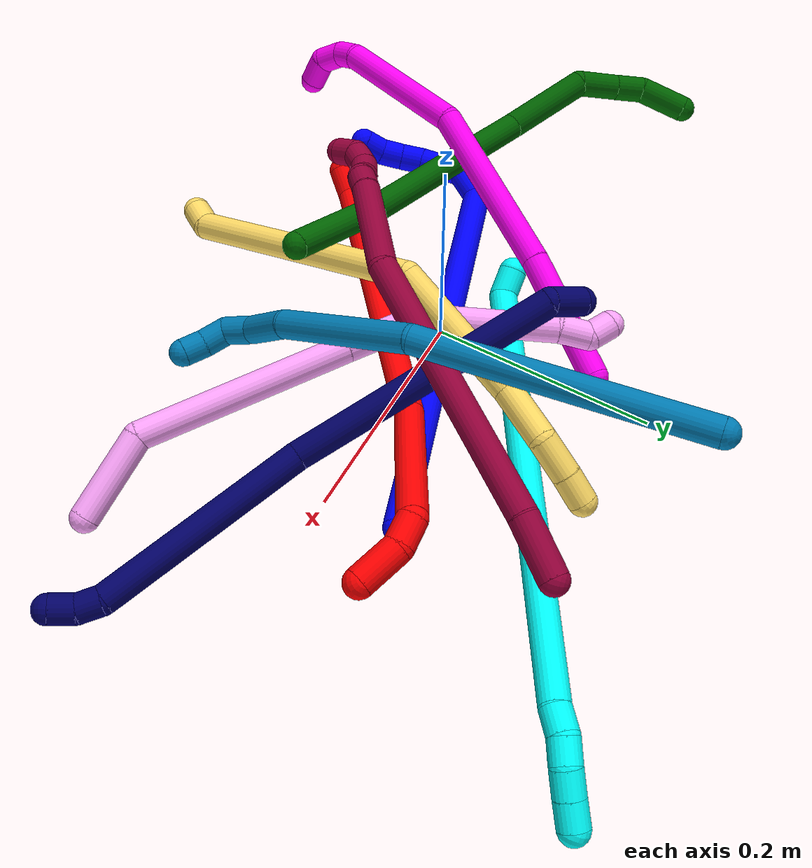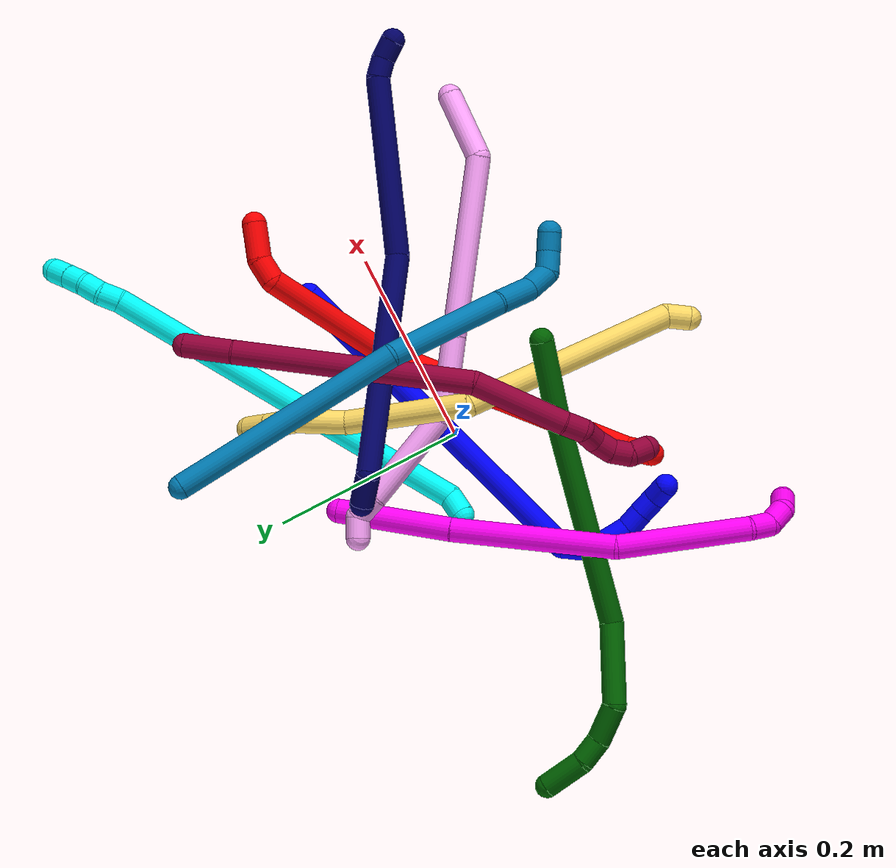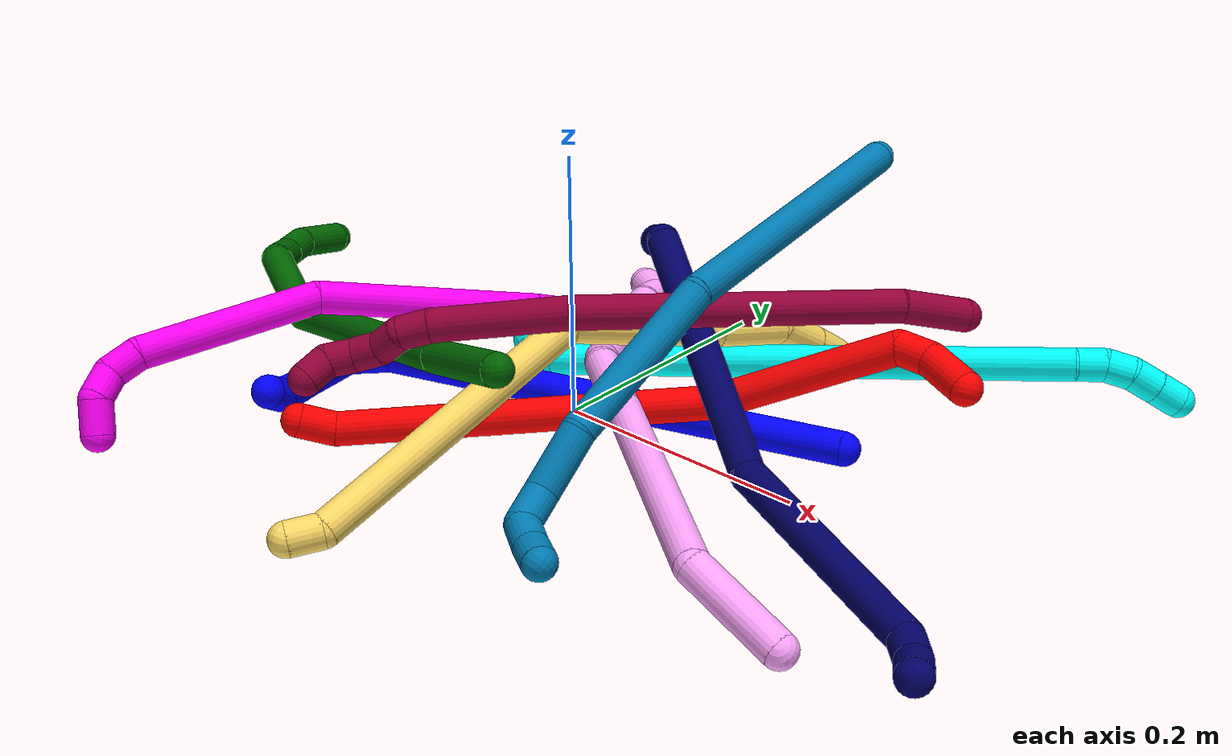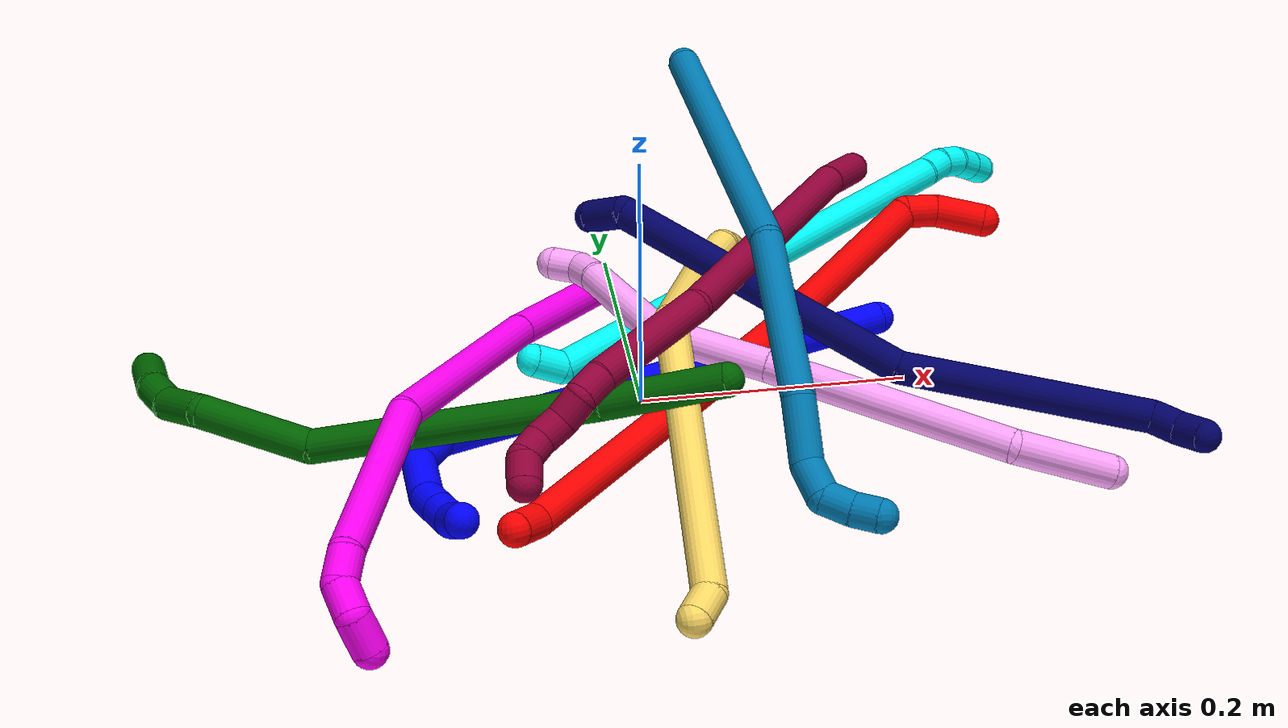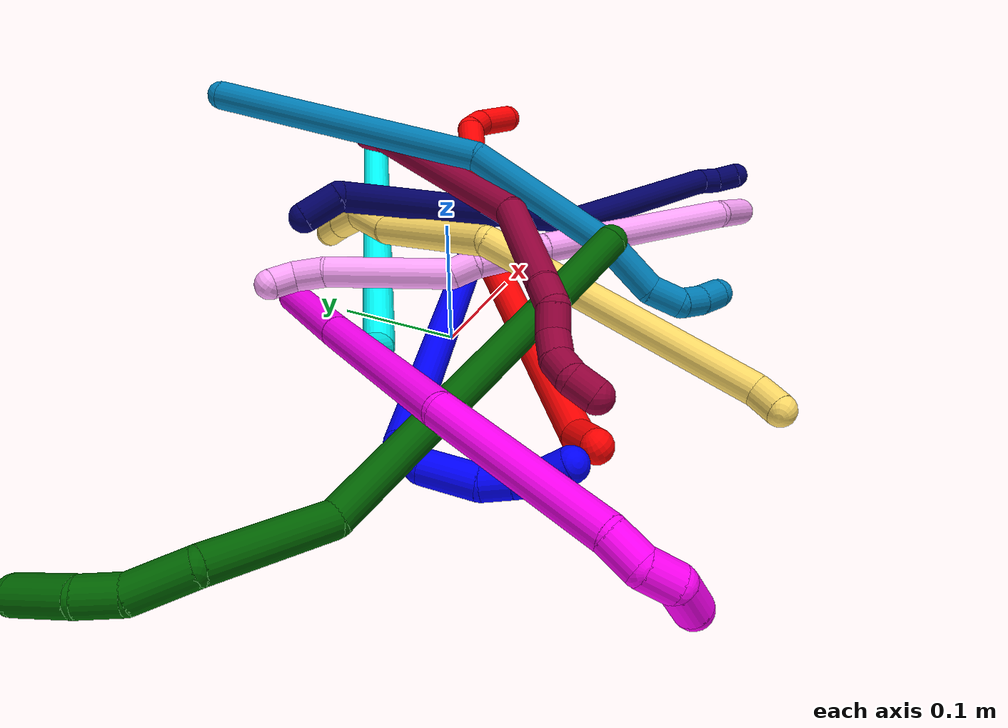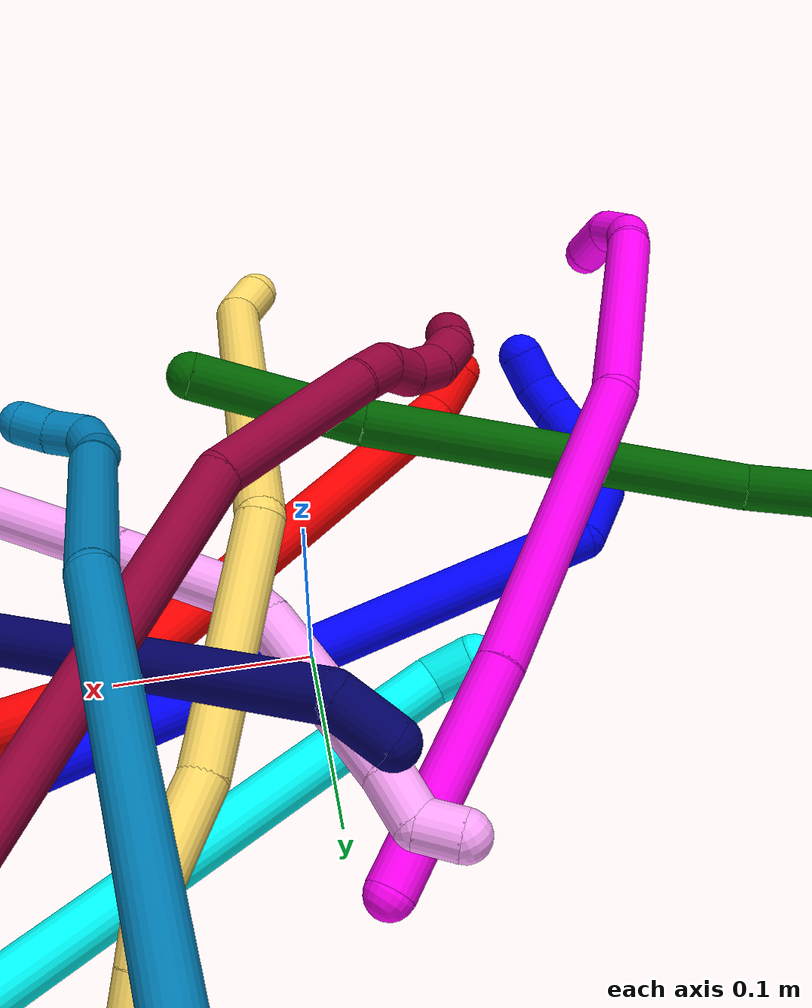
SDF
<sdf version="1.7">
 <world name="default">
  <plugin name="TubeGeneratorPlugin" filename="libtube_generator_plugin.so"/>
  <model name="photoneo_s_sensor">
   <static>1</static>
   <pose>0 0 2 1.57079 1.57079 3.14159</pose>
   <link name="link">
    <inertial><mass>0.1</mass></inertial>
    <sensor name="sensor" type="depth">
     <update_rate>30</update_rate>
     <camera>
      <horizontal_fov>1.22</horizontal_fov>
      <image><width>1920</width><height>1200</height><format>B8G8R8</format></image>
      <clip><near>0.1</near><far>4</far></clip>
      <depth_camera><output>points</output></depth_camera>
     </camera>
     <plugin name="camera_plugin" filename="libgazebo_ros_depth_camera.so">
      <baseline>0.2</baseline>
      <alwaysOn>1</alwaysOn>
      <updateRate>0.0</updateRate>
      <cameraName>camera_ir</cameraName>
      <imageTopicName>/camera/color/image_raw</imageTopicName>
      <cameraInfoTopicName>/camera/color/camera_info</cameraInfoTopicName>
      <depthImageTopicName>/camera/depth/image_raw</depthImageTopicName>
      <depthImageCameraInfoTopicName>/camera/depth/camera_info</depthImageCameraInfoTopicName>
      <pointCloudTopicName>/camera/depth/points</pointCloudTopicName>
      <frameName>fr_optical</frameName>
      <pointCloudCutoff>0.1</pointCloudCutoff>
      <pointCloudCutoffMax>2.0</pointCloudCutoffMax>
      <distortionK1>0</distortionK1>
      <distortionK2>0</distortionK2>
      <distortionK3>0</distortionK3>
      <distortionT1>0</distortionT1>
      <distortionT2>0</distortionT2>
      <CxPrime>0</CxPrime>
      <Cx>0</Cx>
      <Cy>0</Cy>
      <focalLength>0</focalLength>
      <hackBaseline>0</hackBaseline>
     </plugin>
    </sensor>
   </link>
  </model>
  <gravity>0 0 -9.8</gravity>
  <magnetic_field>6e-06 2.3e-05 -4.2e-05</magnetic_field>
  <atmosphere type="adiabatic"/>
  <physics name="default_physics" default="0" type="ode">
   <max_step_size>0.003</max_step_size>
   <real_time_factor>1</real_time_factor>
   <real_time_update_rate>1000</real_time_update_rate>
   <max_contacts>10000</max_contacts>
   <ode>
    <solver>
     <type>quick</type>
     <iters>100</iters>
     <sor>1.3</sor>
     <use_dynamic_moi_rescaling>0</use_dynamic_moi_rescaling>
    </solver>
    <constraints>
     <contact_max_correcting_vel>0</contact_max_correcting_vel>
     <contact_surface_layer>0.001</contact_surface_layer>
     <cfm>0</cfm>
     <erp>0.2</erp>
    </constraints>
   </ode>
  </physics>
  <scene><ambient>0.4 0.4 0.4 1</ambient><background>0.7 0.7 0.7 1</background><shadows>0</shadows></scene>
  <audio><device>default</device></audio>
  <spherical_coordinates>
   <surface_model>EARTH_WGS84</surface_model>
   <latitude_deg>0</latitude_deg>
   <longitude_deg>0</longitude_deg>
   <elevation>0</elevation>
   <heading_deg>0</heading_deg>
  </spherical_coordinates>
  <model name="bin">
   <static>1</static>
   <link name="bottom">
    <collision name="collision-bottom">
     <pose>0 0 -0.01 0 -0 0</pose>
     <geometry><box><size>0.8 0.6 0.02</size></box></geometry>
     <surface>
      <friction><ode><mu>100</mu><mu2>100</mu2></ode></friction>
      <contact><collide_bitmask>65535</collide_bitmask></contact>
     </surface>
    </collision>
   </link>
   <link name="west_wall">
    <collision name="collision-west_wall">
     <pose>-0.41 0 0.1 0 -0 0</pose>
     <geometry><box><size>0.02 0.6 0.2</size></box></geometry>
     <surface>
      <friction><ode><mu>100</mu><mu2>100</mu2></ode></friction>
      <contact><collide_bitmask>65535</collide_bitmask></contact>
     </surface>
    </collision>
   </link>
   <link name="east_wall">
    <collision name="collision-east_wall">
     <pose>0.41 0 0.1 0 -0 0</pose>
     <geometry><box><size>0.02 0.6 0.2</size></box></geometry>
     <surface>
      <friction><ode><mu>100</mu><mu2>100</mu2></ode></friction>
      <contact><collide_bitmask>65535</collide_bitmask></contact>
     </surface>
    </collision>
   </link>
   <link name="south_wall">
    <collision name="collision-south_wall">
     <pose>0 -0.31 0.1 0 -0 0</pose>
     <geometry><box><size>0.8 0.02 0.2</size></box></geometry>
     <surface>
      <friction><ode><mu>100</mu><mu2>100</mu2></ode></friction>
      <contact><collide_bitmask>65535</collide_bitmask></contact>
     </surface>
    </collision>
   </link>
   <link name="north_wall">
    <collision name="collision-north_wall">
     <pose>0 0.31 0.1 0 -0 0</pose>
     <geometry><box><size>0.8 0.02 0.2</size></box></geometry>
     <surface>
      <friction><ode><mu>100</mu><mu2>100</mu2></ode></friction>
      <contact><collide_bitmask>65535</collide_bitmask></contact>
     </surface>
    </collision>
   </link>
  </model>
  <model name="1">
   <static>0</static>
   <link name="1">
    <collision name="collision-cylinder-e_1_1_4">
     <pose>-0.13863 -0.039307 0.111932 0.337716 -0.86297 -0.156665</pose>
     <geometry><cylinder><radius>0.0125</radius><length>0.364922</length></cylinder></geometry>
     <surface>
      <friction><ode><mu>1.16</mu><mu2>1.16</mu2><slip1>0</slip1><slip2>0</slip2></ode></friction>
      <contact><ode><kp>1e+06</kp><kd>1</kd><max_vel>0</max_vel><min_depth>0.001</min_depth></ode></contact>
     </surface>
    </collision>
    <visual name="visual-cylinder-e_1_1_4">
     <pose>-0.13863 -0.039307 0.111932 0.337716 -0.86297 -0.156665</pose>
     <geometry><cylinder><radius>0.0125</radius><length>0.364922</length></cylinder></geometry>
     <material><ambient>0 0 1 1</ambient></material>
    </visual>
    <collision name="collision-cylinder-e_2_4_5">
     <pose>-0.280774 -0.087796 0.236641 0.623129 -0.219778 -0.071037</pose>
     <geometry><cylinder><radius>0.0125</radius><length>0.032243</length></cylinder></geometry>
     <surface>
      <friction><ode><mu>1.16</mu><mu2>1.16</mu2><slip1>0</slip1><slip2>0</slip2></ode></friction>
      <contact><ode><kp>1e+06</kp><kd>1</kd><max_vel>0</max_vel><min_depth>0.001</min_depth></ode></contact>
     </surface>
    </collision>
    <visual name="visual-cylinder-e_2_4_5">
     <pose>-0.280774 -0.087796 0.236641 0.623129 -0.219778 -0.071037</pose>
     <geometry><cylinder><radius>0.0125</radius><length>0.032243</length></cylinder></geometry>
     <material><ambient>0 0 1 1</ambient></material>
    </visual>
    <collision name="collision-cylinder-e_3_5_6">
     <pose>-0.277468 -0.113228 0.260163 0.986525 0.336753 0.182258</pose>
     <geometry><cylinder><radius>0.0125</radius><length>0.041281</length></cylinder></geometry>
     <surface>
      <friction><ode><mu>1.16</mu><mu2>1.16</mu2><slip1>0</slip1><slip2>0</slip2></ode></friction>
      <contact><ode><kp>1e+06</kp><kd>1</kd><max_vel>0</max_vel><min_depth>0.001</min_depth></ode></contact>
     </surface>
    </collision>
    <visual name="visual-cylinder-e_3_5_6">
     <pose>-0.277468 -0.113228 0.260163 0.986525 0.336753 0.182258</pose>
     <geometry><cylinder><radius>0.0125</radius><length>0.041281</length></cylinder></geometry>
     <material><ambient>0 0 1 1</ambient></material>
    </visual>
    <collision name="collision-cylinder-e_4_6_7">
     <pose>-0.263941 -0.135863 0.275853 0.911928 0.693061 0.350557</pose>
     <geometry><cylinder><radius>0.0125</radius><length>0.020996</length></cylinder></geometry>
     <surface>
      <friction><ode><mu>1.16</mu><mu2>1.16</mu2><slip1>0</slip1><slip2>0</slip2></ode></friction>
      <contact><ode><kp>1e+06</kp><kd>1</kd><max_vel>0</max_vel><min_depth>0.001</min_depth></ode></contact>
     </surface>
    </collision>
    <visual name="visual-cylinder-e_4_6_7">
     <pose>-0.263941 -0.135863 0.275853 0.911928 0.693061 0.350557</pose>
     <geometry><cylinder><radius>0.0125</radius><length>0.020996</length></cylinder></geometry>
     <material><ambient>0 0 1 1</ambient></material>
    </visual>
    <collision name="collision-cylinder-e_5_7_8">
     <pose>-0.250808 -0.148186 0.286008 0.850583 0.682861 0.319161</pose>
     <geometry><cylinder><radius>0.0125</radius><length>0.020367</length></cylinder></geometry>
     <surface>
      <friction><ode><mu>1.16</mu><mu2>1.16</mu2><slip1>0</slip1><slip2>0</slip2></ode></friction>
      <contact><ode><kp>1e+06</kp><kd>1</kd><max_vel>0</max_vel><min_depth>0.001</min_depth></ode></contact>
     </surface>
    </collision>
    <visual name="visual-cylinder-e_5_7_8">
     <pose>-0.250808 -0.148186 0.286008 0.850583 0.682861 0.319161</pose>
     <geometry><cylinder><radius>0.0125</radius><length>0.020367</length></cylinder></geometry>
     <material><ambient>0 0 1 1</ambient></material>
    </visual>
    <collision name="collision-cylinder-e_6_8_2">
     <pose>-0.237422 -0.156578 0.298108 0.342076 0.760672 0.137893</pose>
     <geometry><cylinder><radius>0.0125</radius><length>0.020191</length></cylinder></geometry>
     <surface>
      <friction><ode><mu>1.16</mu><mu2>1.16</mu2><slip1>0</slip1><slip2>0</slip2></ode></friction>
      <contact><ode><kp>1e+06</kp><kd>1</kd><max_vel>0</max_vel><min_depth>0.001</min_depth></ode></contact>
     </surface>
    </collision>
    <visual name="visual-cylinder-e_6_8_2">
     <pose>-0.237422 -0.156578 0.298108 0.342076 0.760672 0.137893</pose>
     <geometry><cylinder><radius>0.0125</radius><length>0.020191</length></cylinder></geometry>
     <material><ambient>0 0 1 1</ambient></material>
    </visual>
    <collision name="collision-sphere-2">
     <pose>-0.230462 -0.159031 0.304997 0 -0 0</pose>
     <geometry><sphere><radius>0.0125</radius></sphere></geometry>
     <surface>
      <friction><ode><mu>1.16</mu><mu2>1.16</mu2><slip1>0</slip1><slip2>0</slip2></ode></friction>
      <contact><ode><kp>1e+06</kp><kd>1</kd><max_vel>0</max_vel><min_depth>0.001</min_depth></ode></contact>
     </surface>
    </collision>
    <visual name="visual-sphere-2">
     <pose>-0.230462 -0.159031 0.304997 0 -0 0</pose>
     <geometry><sphere><radius>0.0125</radius></sphere></geometry>
     <material><ambient>0 0 1 1</ambient></material>
    </visual>
    <collision name="collision-sphere-4">
     <pose>-0.277259 -0.078614 0.223864 0 -0 0</pose>
     <geometry><sphere><radius>0.0125</radius></sphere></geometry>
     <surface>
      <friction><ode><mu>1.16</mu><mu2>1.16</mu2><slip1>0</slip1><slip2>0</slip2></ode></friction>
      <contact><ode><kp>1e+06</kp><kd>1</kd><max_vel>0</max_vel><min_depth>0.001</min_depth></ode></contact>
     </surface>
    </collision>
    <visual name="visual-sphere-4">
     <pose>-0.277259 -0.078614 0.223864 0 -0 0</pose>
     <geometry><sphere><radius>0.0125</radius></sphere></geometry>
     <material><ambient>0 0 1 1</ambient></material>
    </visual>
    <collision name="collision-sphere-1">
     <geometry><sphere><radius>0.0125</radius></sphere></geometry>
     <surface>
      <friction><ode><mu>1.16</mu><mu2>1.16</mu2><slip1>0</slip1><slip2>0</slip2></ode></friction>
      <contact><ode><kp>1e+06</kp><kd>1</kd><max_vel>0</max_vel><min_depth>0.001</min_depth></ode></contact>
     </surface>
    </collision>
    <visual name="visual-sphere-1">
     <geometry><sphere><radius>0.0125</radius></sphere></geometry>
     <material><ambient>0 0 1 1</ambient></material>
    </visual>
    <collision name="collision-sphere-8">
     <pose>-0.244382 -0.154125 0.291218 0 -0 0</pose>
     <geometry><sphere><radius>0.0125</radius></sphere></geometry>
     <surface>
      <friction><ode><mu>1.16</mu><mu2>1.16</mu2><slip1>0</slip1><slip2>0</slip2></ode></friction>
      <contact><ode><kp>1e+06</kp><kd>1</kd><max_vel>0</max_vel><min_depth>0.001</min_depth></ode></contact>
     </surface>
    </collision>
    <visual name="visual-sphere-8">
     <pose>-0.244382 -0.154125 0.291218 0 -0 0</pose>
     <geometry><sphere><radius>0.0125</radius></sphere></geometry>
     <material><ambient>0 0 1 1</ambient></material>
    </visual>
    <collision name="collision-sphere-5">
     <pose>-0.284289 -0.096978 0.249418 0 -0 0</pose>
     <geometry><sphere><radius>0.0125</radius></sphere></geometry>
     <surface>
      <friction><ode><mu>1.16</mu><mu2>1.16</mu2><slip1>0</slip1><slip2>0</slip2></ode></friction>
      <contact><ode><kp>1e+06</kp><kd>1</kd><max_vel>0</max_vel><min_depth>0.001</min_depth></ode></contact>
     </surface>
    </collision>
    <visual name="visual-sphere-5">
     <pose>-0.284289 -0.096978 0.249418 0 -0 0</pose>
     <geometry><sphere><radius>0.0125</radius></sphere></geometry>
     <material><ambient>0 0 1 1</ambient></material>
    </visual>
    <collision name="collision-sphere-6">
     <pose>-0.270648 -0.129477 0.270909 0 -0 0</pose>
     <geometry><sphere><radius>0.0125</radius></sphere></geometry>
     <surface>
      <friction><ode><mu>1.16</mu><mu2>1.16</mu2><slip1>0</slip1><slip2>0</slip2></ode></friction>
      <contact><ode><kp>1e+06</kp><kd>1</kd><max_vel>0</max_vel><min_depth>0.001</min_depth></ode></contact>
     </surface>
    </collision>
    <visual name="visual-sphere-6">
     <pose>-0.270648 -0.129477 0.270909 0 -0 0</pose>
     <geometry><sphere><radius>0.0125</radius></sphere></geometry>
     <material><ambient>0 0 1 1</ambient></material>
    </visual>
    <collision name="collision-sphere-7">
     <pose>-0.257234 -0.142248 0.280797 0 -0 0</pose>
     <geometry><sphere><radius>0.0125</radius></sphere></geometry>
     <surface>
      <friction><ode><mu>1.16</mu><mu2>1.16</mu2><slip1>0</slip1><slip2>0</slip2></ode></friction>
      <contact><ode><kp>1e+06</kp><kd>1</kd><max_vel>0</max_vel><min_depth>0.001</min_depth></ode></contact>
     </surface>
    </collision>
    <visual name="visual-sphere-7">
     <pose>-0.257234 -0.142248 0.280797 0 -0 0</pose>
     <geometry><sphere><radius>0.0125</radius></sphere></geometry>
     <material><ambient>0 0 1 1</ambient></material>
    </visual>
    <inertial>
     <pose>-0.17308 -0.061762 0.153705 0 -0 0</pose>
     <mass>0.5</mass>
     <inertia>
      <ixx>0.002196</ixx>
      <ixy>0</ixy>
      <ixz>0</ixz>
      <iyy>0.003536</iyy>
      <iyz>0</iyz>
      <izz>0.003993</izz>
     </inertia>
    </inertial>
   </link>
   <pose>0.195805 0.067529 0.011492 0.768858 -0.36561 -0.31183</pose>
  </model>
  <model name="2">
   <static>0</static>
   <link name="2">
    <collision name="collision-cylinder-e_1_1_4">
     <pose>0.00579 0.012523 -0.000291 -1.59406 0.432994 -0.442858</pose>
     <geometry><cylinder><radius>0.0125</radius><length>0.027599</length></cylinder></geometry>
     <surface>
      <friction><ode><mu>1.16</mu><mu2>1.16</mu2><slip1>0</slip1><slip2>0</slip2></ode></friction>
      <contact><ode><kp>1e+06</kp><kd>1</kd><max_vel>0</max_vel><min_depth>0.001</min_depth></ode></contact>
     </surface>
    </collision>
    <visual name="visual-cylinder-e_1_1_4">
     <pose>0.00579 0.012523 -0.000291 -1.59406 0.432994 -0.442858</pose>
     <geometry><cylinder><radius>0.0125</radius><length>0.027599</length></cylinder></geometry>
     <material><ambient>1 0 0 1</ambient></material>
    </visual>
    <collision name="collision-cylinder-e_2_4_5">
     <pose>0.100449 0.119313 0.037824 -1.18391 0.717724 -0.494125</pose>
     <geometry><cylinder><radius>0.0125</radius><length>0.270252</length></cylinder></geometry>
     <surface>
      <friction><ode><mu>1.16</mu><mu2>1.16</mu2><slip1>0</slip1><slip2>0</slip2></ode></friction>
      <contact><ode><kp>1e+06</kp><kd>1</kd><max_vel>0</max_vel><min_depth>0.001</min_depth></ode></contact>
     </surface>
    </collision>
    <visual name="visual-cylinder-e_2_4_5">
     <pose>0.100449 0.119313 0.037824 -1.18391 0.717724 -0.494125</pose>
     <geometry><cylinder><radius>0.0125</radius><length>0.270252</length></cylinder></geometry>
     <material><ambient>1 0 0 1</ambient></material>
    </visual>
    <collision name="collision-cylinder-e_3_5_6">
     <pose>0.244557 0.241364 0.108525 -0.710474 0.913865 -0.360802</pose>
     <geometry><cylinder><radius>0.0125</radius><length>0.139516</length></cylinder></geometry>
     <surface>
      <friction><ode><mu>1.16</mu><mu2>1.16</mu2><slip1>0</slip1><slip2>0</slip2></ode></friction>
      <contact><ode><kp>1e+06</kp><kd>1</kd><max_vel>0</max_vel><min_depth>0.001</min_depth></ode></contact>
     </surface>
    </collision>
    <visual name="visual-cylinder-e_3_5_6">
     <pose>0.244557 0.241364 0.108525 -0.710474 0.913865 -0.360802</pose>
     <geometry><cylinder><radius>0.0125</radius><length>0.139516</length></cylinder></geometry>
     <material><ambient>1 0 0 1</ambient></material>
    </visual>
    <collision name="collision-cylinder-e_4_6_7">
     <pose>0.311324 0.273181 0.138852 -2.0244 1.19965 -1.66072</pose>
     <geometry><cylinder><radius>0.0125</radius><length>0.02474</length></cylinder></geometry>
     <surface>
      <friction><ode><mu>1.16</mu><mu2>1.16</mu2><slip1>0</slip1><slip2>0</slip2></ode></friction>
      <contact><ode><kp>1e+06</kp><kd>1</kd><max_vel>0</max_vel><min_depth>0.001</min_depth></ode></contact>
     </surface>
    </collision>
    <visual name="visual-cylinder-e_4_6_7">
     <pose>0.311324 0.273181 0.138852 -2.0244 1.19965 -1.66072</pose>
     <geometry><cylinder><radius>0.0125</radius><length>0.02474</length></cylinder></geometry>
     <material><ambient>1 0 0 1</ambient></material>
    </visual>
    <collision name="collision-cylinder-e_5_7_2">
     <pose>0.340233 0.277027 0.129348 3.11687 1.16149 3.10393</pose>
     <geometry><cylinder><radius>0.0125</radius><length>0.037892</length></cylinder></geometry>
     <surface>
      <friction><ode><mu>1.16</mu><mu2>1.16</mu2><slip1>0</slip1><slip2>0</slip2></ode></friction>
      <contact><ode><kp>1e+06</kp><kd>1</kd><max_vel>0</max_vel><min_depth>0.001</min_depth></ode></contact>
     </surface>
    </collision>
    <visual name="visual-cylinder-e_5_7_2">
     <pose>0.340233 0.277027 0.129348 3.11687 1.16149 3.10393</pose>
     <geometry><cylinder><radius>0.0125</radius><length>0.037892</length></cylinder></geometry>
     <material><ambient>1 0 0 1</ambient></material>
    </visual>
    <collision name="collision-sphere-2">
     <pose>0.357614 0.276841 0.12181 0 -0 0</pose>
     <geometry><sphere><radius>0.0125</radius></sphere></geometry>
     <surface>
      <friction><ode><mu>1.16</mu><mu2>1.16</mu2><slip1>0</slip1><slip2>0</slip2></ode></friction>
      <contact><ode><kp>1e+06</kp><kd>1</kd><max_vel>0</max_vel><min_depth>0.001</min_depth></ode></contact>
     </surface>
    </collision>
    <visual name="visual-sphere-2">
     <pose>0.357614 0.276841 0.12181 0 -0 0</pose>
     <geometry><sphere><radius>0.0125</radius></sphere></geometry>
     <material><ambient>1 0 0 1</ambient></material>
    </visual>
    <collision name="collision-sphere-7">
     <pose>0.322852 0.277213 0.136886 0 -0 0</pose>
     <geometry><sphere><radius>0.0125</radius></sphere></geometry>
     <surface>
      <friction><ode><mu>1.16</mu><mu2>1.16</mu2><slip1>0</slip1><slip2>0</slip2></ode></friction>
      <contact><ode><kp>1e+06</kp><kd>1</kd><max_vel>0</max_vel><min_depth>0.001</min_depth></ode></contact>
     </surface>
    </collision>
    <visual name="visual-sphere-7">
     <pose>0.322852 0.277213 0.136886 0 -0 0</pose>
     <geometry><sphere><radius>0.0125</radius></sphere></geometry>
     <material><ambient>1 0 0 1</ambient></material>
    </visual>
    <collision name="collision-sphere-6">
     <pose>0.299796 0.269148 0.140818 0 -0 0</pose>
     <geometry><sphere><radius>0.0125</radius></sphere></geometry>
     <surface>
      <friction><ode><mu>1.16</mu><mu2>1.16</mu2><slip1>0</slip1><slip2>0</slip2></ode></friction>
      <contact><ode><kp>1e+06</kp><kd>1</kd><max_vel>0</max_vel><min_depth>0.001</min_depth></ode></contact>
     </surface>
    </collision>
    <visual name="visual-sphere-6">
     <pose>0.299796 0.269148 0.140818 0 -0 0</pose>
     <geometry><sphere><radius>0.0125</radius></sphere></geometry>
     <material><ambient>1 0 0 1</ambient></material>
    </visual>
    <collision name="collision-sphere-5">
     <pose>0.189318 0.21358 0.076231 0 -0 0</pose>
     <geometry><sphere><radius>0.0125</radius></sphere></geometry>
     <surface>
      <friction><ode><mu>1.16</mu><mu2>1.16</mu2><slip1>0</slip1><slip2>0</slip2></ode></friction>
      <contact><ode><kp>1e+06</kp><kd>1</kd><max_vel>0</max_vel><min_depth>0.001</min_depth></ode></contact>
     </surface>
    </collision>
    <visual name="visual-sphere-5">
     <pose>0.189318 0.21358 0.076231 0 -0 0</pose>
     <geometry><sphere><radius>0.0125</radius></sphere></geometry>
     <material><ambient>1 0 0 1</ambient></material>
    </visual>
    <collision name="collision-sphere-1">
     <geometry><sphere><radius>0.0125</radius></sphere></geometry>
     <surface>
      <friction><ode><mu>1.16</mu><mu2>1.16</mu2><slip1>0</slip1><slip2>0</slip2></ode></friction>
      <contact><ode><kp>1e+06</kp><kd>1</kd><max_vel>0</max_vel><min_depth>0.001</min_depth></ode></contact>
     </surface>
    </collision>
    <visual name="visual-sphere-1">
     <geometry><sphere><radius>0.0125</radius></sphere></geometry>
     <material><ambient>1 0 0 1</ambient></material>
    </visual>
    <collision name="collision-sphere-4">
     <pose>0.01158 0.025045 -0.000583 0 -0 0</pose>
     <geometry><sphere><radius>0.0125</radius></sphere></geometry>
     <surface>
      <friction><ode><mu>1.16</mu><mu2>1.16</mu2><slip1>0</slip1><slip2>0</slip2></ode></friction>
      <contact><ode><kp>1e+06</kp><kd>1</kd><max_vel>0</max_vel><min_depth>0.001</min_depth></ode></contact>
     </surface>
    </collision>
    <visual name="visual-sphere-4">
     <pose>0.01158 0.025045 -0.000583 0 -0 0</pose>
     <geometry><sphere><radius>0.0125</radius></sphere></geometry>
     <material><ambient>1 0 0 1</ambient></material>
    </visual>
    <inertial>
     <pose>0.164041 0.16704 0.067383 0 -0 0</pose>
     <mass>0.5</mass>
     <inertia>
      <ixx>0.000615</ixx>
      <ixy>0</ixy>
      <ixz>0</ixz>
      <iyy>0.000622</iyy>
      <iyz>0</iyz>
      <izz>-0.002522</izz>
     </inertia>
    </inertial>
   </link>
   <pose>-0.11045 -0.168459 0.02121 -0.47671 -0.222502 -0.133041</pose>
  </model>
  <model name="3">
   <static>0</static>
   <link name="3">
    <collision name="collision-cylinder-e_1_1_4">
     <pose>0.001082 0.001786 0.012099 -0.146581 0.088263 -0.006485</pose>
     <geometry><cylinder><radius>0.0125</radius><length>0.024556</length></cylinder></geometry>
     <surface>
      <friction><ode><mu>1.16</mu><mu2>1.16</mu2><slip1>0</slip1><slip2>0</slip2></ode></friction>
      <contact><ode><kp>1e+06</kp><kd>1</kd><max_vel>0</max_vel><min_depth>0.001</min_depth></ode></contact>
     </surface>
    </collision>
    <visual name="visual-cylinder-e_1_1_4">
     <pose>0.001082 0.001786 0.012099 -0.146581 0.088263 -0.006485</pose>
     <geometry><cylinder><radius>0.0125</radius><length>0.024556</length></cylinder></geometry>
     <material><ambient>0.003922 1 0.996078 1</ambient></material>
    </visual>
    <collision name="collision-cylinder-e_2_4_5">
     <pose>0.130586 0.066232 0.15812 -0.437625 0.715168 -0.165797</pose>
     <geometry><cylinder><radius>0.0125</radius><length>0.39168</length></cylinder></geometry>
     <surface>
      <friction><ode><mu>1.16</mu><mu2>1.16</mu2><slip1>0</slip1><slip2>0</slip2></ode></friction>
      <contact><ode><kp>1e+06</kp><kd>1</kd><max_vel>0</max_vel><min_depth>0.001</min_depth></ode></contact>
     </surface>
    </collision>
    <visual name="visual-cylinder-e_2_4_5">
     <pose>0.130586 0.066232 0.15812 -0.437625 0.715168 -0.165797</pose>
     <geometry><cylinder><radius>0.0125</radius><length>0.39168</length></cylinder></geometry>
     <material><ambient>0.003922 1 0.996078 1</ambient></material>
    </visual>
    <collision name="collision-cylinder-e_3_5_6">
     <pose>0.266872 0.130599 0.299088 -0.237711 0.826092 -0.104576</pose>
     <geometry><cylinder><radius>0.0125</radius><length>0.021393</length></cylinder></geometry>
     <surface>
      <friction><ode><mu>1.16</mu><mu2>1.16</mu2><slip1>0</slip1><slip2>0</slip2></ode></friction>
      <contact><ode><kp>1e+06</kp><kd>1</kd><max_vel>0</max_vel><min_depth>0.001</min_depth></ode></contact>
     </surface>
    </collision>
    <visual name="visual-cylinder-e_3_5_6">
     <pose>0.266872 0.130599 0.299088 -0.237711 0.826092 -0.104576</pose>
     <geometry><cylinder><radius>0.0125</radius><length>0.021393</length></cylinder></geometry>
     <material><ambient>0.003922 1 0.996078 1</ambient></material>
    </visual>
    <collision name="collision-cylinder-e_4_6_7">
     <pose>0.280119 0.133026 0.314747 -0.083395 0.556944 -0.023855</pose>
     <geometry><cylinder><radius>0.0125</radius><length>0.020364</length></cylinder></geometry>
     <surface>
      <friction><ode><mu>1.16</mu><mu2>1.16</mu2><slip1>0</slip1><slip2>0</slip2></ode></friction>
      <contact><ode><kp>1e+06</kp><kd>1</kd><max_vel>0</max_vel><min_depth>0.001</min_depth></ode></contact>
     </surface>
    </collision>
    <visual name="visual-cylinder-e_4_6_7">
     <pose>0.280119 0.133026 0.314747 -0.083395 0.556944 -0.023855</pose>
     <geometry><cylinder><radius>0.0125</radius><length>0.020364</length></cylinder></geometry>
     <material><ambient>0.003922 1 0.996078 1</ambient></material>
    </visual>
    <collision name="collision-cylinder-e_5_7_8">
     <pose>0.289921 0.131762 0.332658 0.210317 0.435187 0.046663</pose>
     <geometry><cylinder><radius>0.0125</radius><length>0.020969</length></cylinder></geometry>
     <surface>
      <friction><ode><mu>1.16</mu><mu2>1.16</mu2><slip1>0</slip1><slip2>0</slip2></ode></friction>
      <contact><ode><kp>1e+06</kp><kd>1</kd><max_vel>0</max_vel><min_depth>0.001</min_depth></ode></contact>
     </surface>
    </collision>
    <visual name="visual-cylinder-e_5_7_8">
     <pose>0.289921 0.131762 0.332658 0.210317 0.435187 0.046663</pose>
     <geometry><cylinder><radius>0.0125</radius><length>0.020969</length></cylinder></geometry>
     <material><ambient>0.003922 1 0.996078 1</ambient></material>
    </visual>
    <collision name="collision-cylinder-e_6_8_2">
     <pose>0.298843 0.12749 0.351184 0.242874 0.442176 0.054845</pose>
     <geometry><cylinder><radius>0.0125</radius><length>0.021037</length></cylinder></geometry>
     <surface>
      <friction><ode><mu>1.16</mu><mu2>1.16</mu2><slip1>0</slip1><slip2>0</slip2></ode></friction>
      <contact><ode><kp>1e+06</kp><kd>1</kd><max_vel>0</max_vel><min_depth>0.001</min_depth></ode></contact>
     </surface>
    </collision>
    <visual name="visual-cylinder-e_6_8_2">
     <pose>0.298843 0.12749 0.351184 0.242874 0.442176 0.054845</pose>
     <geometry><cylinder><radius>0.0125</radius><length>0.021037</length></cylinder></geometry>
     <material><ambient>0.003922 1 0.996078 1</ambient></material>
    </visual>
    <collision name="collision-sphere-2">
     <pose>0.303344 0.125204 0.360412 0 -0 0</pose>
     <geometry><sphere><radius>0.0125</radius></sphere></geometry>
     <surface>
      <friction><ode><mu>1.16</mu><mu2>1.16</mu2><slip1>0</slip1><slip2>0</slip2></ode></friction>
      <contact><ode><kp>1e+06</kp><kd>1</kd><max_vel>0</max_vel><min_depth>0.001</min_depth></ode></contact>
     </surface>
    </collision>
    <visual name="visual-sphere-2">
     <pose>0.303344 0.125204 0.360412 0 -0 0</pose>
     <geometry><sphere><radius>0.0125</radius></sphere></geometry>
     <material><ambient>0.003922 1 0.996078 1</ambient></material>
    </visual>
    <collision name="collision-sphere-4">
     <pose>0.002165 0.003573 0.024198 0 -0 0</pose>
     <geometry><sphere><radius>0.0125</radius></sphere></geometry>
     <surface>
      <friction><ode><mu>1.16</mu><mu2>1.16</mu2><slip1>0</slip1><slip2>0</slip2></ode></friction>
      <contact><ode><kp>1e+06</kp><kd>1</kd><max_vel>0</max_vel><min_depth>0.001</min_depth></ode></contact>
     </surface>
    </collision>
    <visual name="visual-sphere-4">
     <pose>0.002165 0.003573 0.024198 0 -0 0</pose>
     <geometry><sphere><radius>0.0125</radius></sphere></geometry>
     <material><ambient>0.003922 1 0.996078 1</ambient></material>
    </visual>
    <collision name="collision-sphere-1">
     <geometry><sphere><radius>0.0125</radius></sphere></geometry>
     <surface>
      <friction><ode><mu>1.16</mu><mu2>1.16</mu2><slip1>0</slip1><slip2>0</slip2></ode></friction>
      <contact><ode><kp>1e+06</kp><kd>1</kd><max_vel>0</max_vel><min_depth>0.001</min_depth></ode></contact>
     </surface>
    </collision>
    <visual name="visual-sphere-1">
     <geometry><sphere><radius>0.0125</radius></sphere></geometry>
     <material><ambient>0.003922 1 0.996078 1</ambient></material>
    </visual>
    <collision name="collision-sphere-8">
     <pose>0.294342 0.129777 0.341956 0 -0 0</pose>
     <geometry><sphere><radius>0.0125</radius></sphere></geometry>
     <surface>
      <friction><ode><mu>1.16</mu><mu2>1.16</mu2><slip1>0</slip1><slip2>0</slip2></ode></friction>
      <contact><ode><kp>1e+06</kp><kd>1</kd><max_vel>0</max_vel><min_depth>0.001</min_depth></ode></contact>
     </surface>
    </collision>
    <visual name="visual-sphere-8">
     <pose>0.294342 0.129777 0.341956 0 -0 0</pose>
     <geometry><sphere><radius>0.0125</radius></sphere></geometry>
     <material><ambient>0.003922 1 0.996078 1</ambient></material>
    </visual>
    <collision name="collision-sphere-5">
     <pose>0.259007 0.128892 0.292042 0 -0 0</pose>
     <geometry><sphere><radius>0.0125</radius></sphere></geometry>
     <surface>
      <friction><ode><mu>1.16</mu><mu2>1.16</mu2><slip1>0</slip1><slip2>0</slip2></ode></friction>
      <contact><ode><kp>1e+06</kp><kd>1</kd><max_vel>0</max_vel><min_depth>0.001</min_depth></ode></contact>
     </surface>
    </collision>
    <visual name="visual-sphere-5">
     <pose>0.259007 0.128892 0.292042 0 -0 0</pose>
     <geometry><sphere><radius>0.0125</radius></sphere></geometry>
     <material><ambient>0.003922 1 0.996078 1</ambient></material>
    </visual>
    <collision name="collision-sphere-6">
     <pose>0.274737 0.132306 0.306134 0 -0 0</pose>
     <geometry><sphere><radius>0.0125</radius></sphere></geometry>
     <surface>
      <friction><ode><mu>1.16</mu><mu2>1.16</mu2><slip1>0</slip1><slip2>0</slip2></ode></friction>
      <contact><ode><kp>1e+06</kp><kd>1</kd><max_vel>0</max_vel><min_depth>0.001</min_depth></ode></contact>
     </surface>
    </collision>
    <visual name="visual-sphere-6">
     <pose>0.274737 0.132306 0.306134 0 -0 0</pose>
     <geometry><sphere><radius>0.0125</radius></sphere></geometry>
     <material><ambient>0.003922 1 0.996078 1</ambient></material>
    </visual>
    <collision name="collision-sphere-7">
     <pose>0.285501 0.133746 0.32336 0 -0 0</pose>
     <geometry><sphere><radius>0.0125</radius></sphere></geometry>
     <surface>
      <friction><ode><mu>1.16</mu><mu2>1.16</mu2><slip1>0</slip1><slip2>0</slip2></ode></friction>
      <contact><ode><kp>1e+06</kp><kd>1</kd><max_vel>0</max_vel><min_depth>0.001</min_depth></ode></contact>
     </surface>
    </collision>
    <visual name="visual-sphere-7">
     <pose>0.285501 0.133746 0.32336 0 -0 0</pose>
     <geometry><sphere><radius>0.0125</radius></sphere></geometry>
     <material><ambient>0.003922 1 0.996078 1</ambient></material>
    </visual>
    <inertial>
     <pose>0.149909 0.073867 0.178802 0 -0 0</pose>
     <mass>0.5</mass>
     <inertia>
      <ixx>0.003145</ixx>
      <ixy>0</ixy>
      <ixz>0</ixz>
      <iyy>0.00411</iyy>
      <iyz>0</iyz>
      <izz>-0.004876</izz>
     </inertia>
    </inertial>
   </link>
   <pose>-0.076648 0.032303 0.022925 2.22522 -0.342615 1.38975</pose>
  </model>
  <model name="4">
   <static>0</static>
   <link name="4">
    <collision name="collision-cylinder-e_1_1_4">
     <pose>-0.037546 0.007259 -0.001847 -1.81993 -1.37387 1.62431</pose>
     <geometry><cylinder><radius>0.0125</radius><length>0.076571</length></cylinder></geometry>
     <surface>
      <friction><ode><mu>1.16</mu><mu2>1.16</mu2><slip1>0</slip1><slip2>0</slip2></ode></friction>
      <contact><ode><kp>1e+06</kp><kd>1</kd><max_vel>0</max_vel><min_depth>0.001</min_depth></ode></contact>
     </surface>
    </collision>
    <visual name="visual-cylinder-e_1_1_4">
     <pose>-0.037546 0.007259 -0.001847 -1.81993 -1.37387 1.62431</pose>
     <geometry><cylinder><radius>0.0125</radius><length>0.076571</length></cylinder></geometry>
     <material><ambient>1 0.65098 0.996078 1</ambient></material>
    </visual>
    <collision name="collision-cylinder-e_2_4_5">
     <pose>-0.142182 0.058773 -0.05067 -2.38602 -0.804787 1.64073</pose>
     <geometry><cylinder><radius>0.0125</radius><length>0.186187</length></cylinder></geometry>
     <surface>
      <friction><ode><mu>1.16</mu><mu2>1.16</mu2><slip1>0</slip1><slip2>0</slip2></ode></friction>
      <contact><ode><kp>1e+06</kp><kd>1</kd><max_vel>0</max_vel><min_depth>0.001</min_depth></ode></contact>
     </surface>
    </collision>
    <visual name="visual-cylinder-e_2_4_5">
     <pose>-0.142182 0.058773 -0.05067 -2.38602 -0.804787 1.64073</pose>
     <geometry><cylinder><radius>0.0125</radius><length>0.186187</length></cylinder></geometry>
     <material><ambient>1 0.65098 0.996078 1</ambient></material>
    </visual>
    <collision name="collision-cylinder-e_3_5_6">
     <pose>-0.232636 0.11798 -0.114887 -2.42714 -0.797126 1.69116</pose>
     <geometry><cylinder><radius>0.0125</radius><length>0.065319</length></cylinder></geometry>
     <surface>
      <friction><ode><mu>1.16</mu><mu2>1.16</mu2><slip1>0</slip1><slip2>0</slip2></ode></friction>
      <contact><ode><kp>1e+06</kp><kd>1</kd><max_vel>0</max_vel><min_depth>0.001</min_depth></ode></contact>
     </surface>
    </collision>
    <visual name="visual-cylinder-e_3_5_6">
     <pose>-0.232636 0.11798 -0.114887 -2.42714 -0.797126 1.69116</pose>
     <geometry><cylinder><radius>0.0125</radius><length>0.065319</length></cylinder></geometry>
     <material><ambient>1 0.65098 0.996078 1</ambient></material>
    </visual>
    <collision name="collision-cylinder-e_4_6_7">
     <pose>-0.260666 0.137012 -0.140408 -2.68382 -0.468122 1.59397</pose>
     <geometry><cylinder><radius>0.0125</radius><length>0.020688</length></cylinder></geometry>
     <surface>
      <friction><ode><mu>1.16</mu><mu2>1.16</mu2><slip1>0</slip1><slip2>0</slip2></ode></friction>
      <contact><ode><kp>1e+06</kp><kd>1</kd><max_vel>0</max_vel><min_depth>0.001</min_depth></ode></contact>
     </surface>
    </collision>
    <visual name="visual-cylinder-e_4_6_7">
     <pose>-0.260666 0.137012 -0.140408 -2.68382 -0.468122 1.59397</pose>
     <geometry><cylinder><radius>0.0125</radius><length>0.020688</length></cylinder></geometry>
     <material><ambient>1 0.65098 0.996078 1</ambient></material>
    </visual>
    <collision name="collision-cylinder-e_5_7_8">
     <pose>-0.278882 0.179672 -0.179457 -2.24404 -0.267951 0.545823</pose>
     <geometry><cylinder><radius>0.0125</radius><length>0.102347</length></cylinder></geometry>
     <surface>
      <friction><ode><mu>1.16</mu><mu2>1.16</mu2><slip1>0</slip1><slip2>0</slip2></ode></friction>
      <contact><ode><kp>1e+06</kp><kd>1</kd><max_vel>0</max_vel><min_depth>0.001</min_depth></ode></contact>
     </surface>
    </collision>
    <visual name="visual-cylinder-e_5_7_8">
     <pose>-0.278882 0.179672 -0.179457 -2.24404 -0.267951 0.545823</pose>
     <geometry><cylinder><radius>0.0125</radius><length>0.102347</length></cylinder></geometry>
     <material><ambient>1 0.65098 0.996078 1</ambient></material>
    </visual>
    <collision name="collision-cylinder-e_6_8_9">
     <pose>-0.294583 0.226952 -0.220343 -2.43132 -0.159927 0.425607</pose>
     <geometry><cylinder><radius>0.0125</radius><length>0.02703</length></cylinder></geometry>
     <surface>
      <friction><ode><mu>1.16</mu><mu2>1.16</mu2><slip1>0</slip1><slip2>0</slip2></ode></friction>
      <contact><ode><kp>1e+06</kp><kd>1</kd><max_vel>0</max_vel><min_depth>0.001</min_depth></ode></contact>
     </surface>
    </collision>
    <visual name="visual-cylinder-e_6_8_9">
     <pose>-0.294583 0.226952 -0.220343 -2.43132 -0.159927 0.425607</pose>
     <geometry><cylinder><radius>0.0125</radius><length>0.02703</length></cylinder></geometry>
     <material><ambient>1 0.65098 0.996078 1</ambient></material>
    </visual>
    <collision name="collision-cylinder-e_7_9_2">
     <pose>-0.305424 0.239327 -0.235977 -2.55397 -0.918995 2.04397</pose>
     <geometry><cylinder><radius>0.0125</radius><length>0.021858</length></cylinder></geometry>
     <surface>
      <friction><ode><mu>1.16</mu><mu2>1.16</mu2><slip1>0</slip1><slip2>0</slip2></ode></friction>
      <contact><ode><kp>1e+06</kp><kd>1</kd><max_vel>0</max_vel><min_depth>0.001</min_depth></ode></contact>
     </surface>
    </collision>
    <visual name="visual-cylinder-e_7_9_2">
     <pose>-0.305424 0.239327 -0.235977 -2.55397 -0.918995 2.04397</pose>
     <geometry><cylinder><radius>0.0125</radius><length>0.021858</length></cylinder></geometry>
     <material><ambient>1 0.65098 0.996078 1</ambient></material>
    </visual>
    <collision name="collision-sphere-2">
     <pose>-0.314112 0.243002 -0.241494 0 -0 0</pose>
     <geometry><sphere><radius>0.0125</radius></sphere></geometry>
     <surface>
      <friction><ode><mu>1.16</mu><mu2>1.16</mu2><slip1>0</slip1><slip2>0</slip2></ode></friction>
      <contact><ode><kp>1e+06</kp><kd>1</kd><max_vel>0</max_vel><min_depth>0.001</min_depth></ode></contact>
     </surface>
    </collision>
    <visual name="visual-sphere-2">
     <pose>-0.314112 0.243002 -0.241494 0 -0 0</pose>
     <geometry><sphere><radius>0.0125</radius></sphere></geometry>
     <material><ambient>1 0.65098 0.996078 1</ambient></material>
    </visual>
    <collision name="collision-sphere-9">
     <pose>-0.296735 0.235651 -0.230459 0 -0 0</pose>
     <geometry><sphere><radius>0.0125</radius></sphere></geometry>
     <surface>
      <friction><ode><mu>1.16</mu><mu2>1.16</mu2><slip1>0</slip1><slip2>0</slip2></ode></friction>
      <contact><ode><kp>1e+06</kp><kd>1</kd><max_vel>0</max_vel><min_depth>0.001</min_depth></ode></contact>
     </surface>
    </collision>
    <visual name="visual-sphere-9">
     <pose>-0.296735 0.235651 -0.230459 0 -0 0</pose>
     <geometry><sphere><radius>0.0125</radius></sphere></geometry>
     <material><ambient>1 0.65098 0.996078 1</ambient></material>
    </visual>
    <collision name="collision-sphere-4">
     <pose>-0.075091 0.014519 -0.003694 0 -0 0</pose>
     <geometry><sphere><radius>0.0125</radius></sphere></geometry>
     <surface>
      <friction><ode><mu>1.16</mu><mu2>1.16</mu2><slip1>0</slip1><slip2>0</slip2></ode></friction>
      <contact><ode><kp>1e+06</kp><kd>1</kd><max_vel>0</max_vel><min_depth>0.001</min_depth></ode></contact>
     </surface>
    </collision>
    <visual name="visual-sphere-4">
     <pose>-0.075091 0.014519 -0.003694 0 -0 0</pose>
     <geometry><sphere><radius>0.0125</radius></sphere></geometry>
     <material><ambient>1 0.65098 0.996078 1</ambient></material>
    </visual>
    <collision name="collision-sphere-1">
     <geometry><sphere><radius>0.0125</radius></sphere></geometry>
     <surface>
      <friction><ode><mu>1.16</mu><mu2>1.16</mu2><slip1>0</slip1><slip2>0</slip2></ode></friction>
      <contact><ode><kp>1e+06</kp><kd>1</kd><max_vel>0</max_vel><min_depth>0.001</min_depth></ode></contact>
     </surface>
    </collision>
    <visual name="visual-sphere-1">
     <geometry><sphere><radius>0.0125</radius></sphere></geometry>
     <material><ambient>1 0.65098 0.996078 1</ambient></material>
    </visual>
    <collision name="collision-sphere-8">
     <pose>-0.29243 0.218252 -0.210227 0 -0 0</pose>
     <geometry><sphere><radius>0.0125</radius></sphere></geometry>
     <surface>
      <friction><ode><mu>1.16</mu><mu2>1.16</mu2><slip1>0</slip1><slip2>0</slip2></ode></friction>
      <contact><ode><kp>1e+06</kp><kd>1</kd><max_vel>0</max_vel><min_depth>0.001</min_depth></ode></contact>
     </surface>
    </collision>
    <visual name="visual-sphere-8">
     <pose>-0.29243 0.218252 -0.210227 0 -0 0</pose>
     <geometry><sphere><radius>0.0125</radius></sphere></geometry>
     <material><ambient>1 0.65098 0.996078 1</ambient></material>
    </visual>
    <collision name="collision-sphere-5">
     <pose>-0.209273 0.103027 -0.097646 0 -0 0</pose>
     <geometry><sphere><radius>0.0125</radius></sphere></geometry>
     <surface>
      <friction><ode><mu>1.16</mu><mu2>1.16</mu2><slip1>0</slip1><slip2>0</slip2></ode></friction>
      <contact><ode><kp>1e+06</kp><kd>1</kd><max_vel>0</max_vel><min_depth>0.001</min_depth></ode></contact>
     </surface>
    </collision>
    <visual name="visual-sphere-5">
     <pose>-0.209273 0.103027 -0.097646 0 -0 0</pose>
     <geometry><sphere><radius>0.0125</radius></sphere></geometry>
     <material><ambient>1 0.65098 0.996078 1</ambient></material>
    </visual>
    <collision name="collision-sphere-6">
     <pose>-0.255999 0.132932 -0.132127 0 -0 0</pose>
     <geometry><sphere><radius>0.0125</radius></sphere></geometry>
     <surface>
      <friction><ode><mu>1.16</mu><mu2>1.16</mu2><slip1>0</slip1><slip2>0</slip2></ode></friction>
      <contact><ode><kp>1e+06</kp><kd>1</kd><max_vel>0</max_vel><min_depth>0.001</min_depth></ode></contact>
     </surface>
    </collision>
    <visual name="visual-sphere-6">
     <pose>-0.255999 0.132932 -0.132127 0 -0 0</pose>
     <geometry><sphere><radius>0.0125</radius></sphere></geometry>
     <material><ambient>1 0.65098 0.996078 1</ambient></material>
    </visual>
    <collision name="collision-sphere-7">
     <pose>-0.265334 0.141092 -0.148688 0 -0 0</pose>
     <geometry><sphere><radius>0.0125</radius></sphere></geometry>
     <surface>
      <friction><ode><mu>1.16</mu><mu2>1.16</mu2><slip1>0</slip1><slip2>0</slip2></ode></friction>
      <contact><ode><kp>1e+06</kp><kd>1</kd><max_vel>0</max_vel><min_depth>0.001</min_depth></ode></contact>
     </surface>
    </collision>
    <visual name="visual-sphere-7">
     <pose>-0.265334 0.141092 -0.148688 0 -0 0</pose>
     <geometry><sphere><radius>0.0125</radius></sphere></geometry>
     <material><ambient>1 0.65098 0.996078 1</ambient></material>
    </visual>
    <inertial>
     <pose>-0.186234 0.103588 -0.098931 0 -0 0</pose>
     <mass>0.5</mass>
     <inertia>
      <ixx>0.000478</ixx>
      <ixy>0</ixy>
      <ixz>0</ixz>
      <iyy>0.000782</iyy>
      <iyz>0</iyz>
      <izz>0.000107</izz>
     </inertia>
    </inertial>
   </link>
   <pose>0.310767 -0.155032 0.011676 0.598736 0.29198 0.130517</pose>
  </model>
  <model name="5">
   <static>0</static>
   <link name="5">
    <collision name="collision-cylinder-e_1_1_4">
     <pose>0.001194 0.009402 0.007775 -0.879845 0.097573 -0.045955</pose>
     <geometry><cylinder><radius>0.0125</radius><length>0.024517</length></cylinder></geometry>
     <surface>
      <friction><ode><mu>1.16</mu><mu2>1.16</mu2><slip1>0</slip1><slip2>0</slip2></ode></friction>
      <contact><ode><kp>1e+06</kp><kd>1</kd><max_vel>0</max_vel><min_depth>0.001</min_depth></ode></contact>
     </surface>
    </collision>
    <visual name="visual-cylinder-e_1_1_4">
     <pose>0.001194 0.009402 0.007775 -0.879845 0.097573 -0.045955</pose>
     <geometry><cylinder><radius>0.0125</radius><length>0.024517</length></cylinder></geometry>
     <material><ambient>1 0.858824 0.4 1</ambient></material>
    </visual>
    <collision name="collision-cylinder-e_2_4_5">
     <pose>-0.000683 0.13436 0.033129 -1.41983 -0.026271 0.022577</pose>
     <geometry><cylinder><radius>0.0125</radius><length>0.233852</length></cylinder></geometry>
     <surface>
      <friction><ode><mu>1.16</mu><mu2>1.16</mu2><slip1>0</slip1><slip2>0</slip2></ode></friction>
      <contact><ode><kp>1e+06</kp><kd>1</kd><max_vel>0</max_vel><min_depth>0.001</min_depth></ode></contact>
     </surface>
    </collision>
    <visual name="visual-cylinder-e_2_4_5">
     <pose>-0.000683 0.13436 0.033129 -1.41983 -0.026271 0.022577</pose>
     <geometry><cylinder><radius>0.0125</radius><length>0.233852</length></cylinder></geometry>
     <material><ambient>1 0.858824 0.4 1</ambient></material>
    </visual>
    <collision name="collision-cylinder-e_3_5_6">
     <pose>0.027035 0.299154 0.079197 -1.04626 0.4961 -0.290079</pose>
     <geometry><cylinder><radius>0.0125</radius><length>0.129367</length></cylinder></geometry>
     <surface>
      <friction><ode><mu>1.16</mu><mu2>1.16</mu2><slip1>0</slip1><slip2>0</slip2></ode></friction>
      <contact><ode><kp>1e+06</kp><kd>1</kd><max_vel>0</max_vel><min_depth>0.001</min_depth></ode></contact>
     </surface>
    </collision>
    <visual name="visual-cylinder-e_3_5_6">
     <pose>0.027035 0.299154 0.079197 -1.04626 0.4961 -0.290079</pose>
     <geometry><cylinder><radius>0.0125</radius><length>0.129367</length></cylinder></geometry>
     <material><ambient>1 0.858824 0.4 1</ambient></material>
    </visual>
    <collision name="collision-cylinder-e_4_6_7">
     <pose>0.065806 0.367305 0.122965 -0.891285 0.317194 -0.152508</pose>
     <geometry><cylinder><radius>0.0125</radius><length>0.051181</length></cylinder></geometry>
     <surface>
      <friction><ode><mu>1.16</mu><mu2>1.16</mu2><slip1>0</slip1><slip2>0</slip2></ode></friction>
      <contact><ode><kp>1e+06</kp><kd>1</kd><max_vel>0</max_vel><min_depth>0.001</min_depth></ode></contact>
     </surface>
    </collision>
    <visual name="visual-cylinder-e_4_6_7">
     <pose>0.065806 0.367305 0.122965 -0.891285 0.317194 -0.152508</pose>
     <geometry><cylinder><radius>0.0125</radius><length>0.051181</length></cylinder></geometry>
     <material><ambient>1 0.858824 0.4 1</ambient></material>
    </visual>
    <collision name="collision-cylinder-e_5_7_8">
     <pose>0.08638 0.396242 0.144924 -0.982977 0.807565 -0.44969</pose>
     <geometry><cylinder><radius>0.0125</radius><length>0.034852</length></cylinder></geometry>
     <surface>
      <friction><ode><mu>1.16</mu><mu2>1.16</mu2><slip1>0</slip1><slip2>0</slip2></ode></friction>
      <contact><ode><kp>1e+06</kp><kd>1</kd><max_vel>0</max_vel><min_depth>0.001</min_depth></ode></contact>
     </surface>
    </collision>
    <visual name="visual-cylinder-e_5_7_8">
     <pose>0.08638 0.396242 0.144924 -0.982977 0.807565 -0.44969</pose>
     <geometry><cylinder><radius>0.0125</radius><length>0.034852</length></cylinder></geometry>
     <material><ambient>1 0.858824 0.4 1</ambient></material>
    </visual>
    <collision name="collision-cylinder-e_6_8_2">
     <pose>0.108947 0.413131 0.156643 -0.937666 0.864144 -0.458898</pose>
     <geometry><cylinder><radius>0.0125</radius><length>0.026232</length></cylinder></geometry>
     <surface>
      <friction><ode><mu>1.16</mu><mu2>1.16</mu2><slip1>0</slip1><slip2>0</slip2></ode></friction>
      <contact><ode><kp>1e+06</kp><kd>1</kd><max_vel>0</max_vel><min_depth>0.001</min_depth></ode></contact>
     </surface>
    </collision>
    <visual name="visual-cylinder-e_6_8_2">
     <pose>0.108947 0.413131 0.156643 -0.937666 0.864144 -0.458898</pose>
     <geometry><cylinder><radius>0.0125</radius><length>0.026232</length></cylinder></geometry>
     <material><ambient>1 0.858824 0.4 1</ambient></material>
    </visual>
    <collision name="collision-sphere-2">
     <pose>0.118922 0.419997 0.161682 0 -0 0</pose>
     <geometry><sphere><radius>0.0125</radius></sphere></geometry>
     <surface>
      <friction><ode><mu>1.16</mu><mu2>1.16</mu2><slip1>0</slip1><slip2>0</slip2></ode></friction>
      <contact><ode><kp>1e+06</kp><kd>1</kd><max_vel>0</max_vel><min_depth>0.001</min_depth></ode></contact>
     </surface>
    </collision>
    <visual name="visual-sphere-2">
     <pose>0.118922 0.419997 0.161682 0 -0 0</pose>
     <geometry><sphere><radius>0.0125</radius></sphere></geometry>
     <material><ambient>1 0.858824 0.4 1</ambient></material>
    </visual>
    <collision name="collision-sphere-4">
     <pose>0.002388 0.018804 0.01555 0 -0 0</pose>
     <geometry><sphere><radius>0.0125</radius></sphere></geometry>
     <surface>
      <friction><ode><mu>1.16</mu><mu2>1.16</mu2><slip1>0</slip1><slip2>0</slip2></ode></friction>
      <contact><ode><kp>1e+06</kp><kd>1</kd><max_vel>0</max_vel><min_depth>0.001</min_depth></ode></contact>
     </surface>
    </collision>
    <visual name="visual-sphere-4">
     <pose>0.002388 0.018804 0.01555 0 -0 0</pose>
     <geometry><sphere><radius>0.0125</radius></sphere></geometry>
     <material><ambient>1 0.858824 0.4 1</ambient></material>
    </visual>
    <collision name="collision-sphere-1">
     <geometry><sphere><radius>0.0125</radius></sphere></geometry>
     <surface>
      <friction><ode><mu>1.16</mu><mu2>1.16</mu2><slip1>0</slip1><slip2>0</slip2></ode></friction>
      <contact><ode><kp>1e+06</kp><kd>1</kd><max_vel>0</max_vel><min_depth>0.001</min_depth></ode></contact>
     </surface>
    </collision>
    <visual name="visual-sphere-1">
     <geometry><sphere><radius>0.0125</radius></sphere></geometry>
     <material><ambient>1 0.858824 0.4 1</ambient></material>
    </visual>
    <collision name="collision-sphere-8">
     <pose>0.098972 0.406266 0.151604 0 -0 0</pose>
     <geometry><sphere><radius>0.0125</radius></sphere></geometry>
     <surface>
      <friction><ode><mu>1.16</mu><mu2>1.16</mu2><slip1>0</slip1><slip2>0</slip2></ode></friction>
      <contact><ode><kp>1e+06</kp><kd>1</kd><max_vel>0</max_vel><min_depth>0.001</min_depth></ode></contact>
     </surface>
    </collision>
    <visual name="visual-sphere-8">
     <pose>0.098972 0.406266 0.151604 0 -0 0</pose>
     <geometry><sphere><radius>0.0125</radius></sphere></geometry>
     <material><ambient>1 0.858824 0.4 1</ambient></material>
    </visual>
    <collision name="collision-sphere-5">
     <pose>-0.003754 0.249916 0.050708 0 -0 0</pose>
     <geometry><sphere><radius>0.0125</radius></sphere></geometry>
     <surface>
      <friction><ode><mu>1.16</mu><mu2>1.16</mu2><slip1>0</slip1><slip2>0</slip2></ode></friction>
      <contact><ode><kp>1e+06</kp><kd>1</kd><max_vel>0</max_vel><min_depth>0.001</min_depth></ode></contact>
     </surface>
    </collision>
    <visual name="visual-sphere-5">
     <pose>-0.003754 0.249916 0.050708 0 -0 0</pose>
     <geometry><sphere><radius>0.0125</radius></sphere></geometry>
     <material><ambient>1 0.858824 0.4 1</ambient></material>
    </visual>
    <collision name="collision-sphere-6">
     <pose>0.057824 0.348392 0.107686 0 -0 0</pose>
     <geometry><sphere><radius>0.0125</radius></sphere></geometry>
     <surface>
      <friction><ode><mu>1.16</mu><mu2>1.16</mu2><slip1>0</slip1><slip2>0</slip2></ode></friction>
      <contact><ode><kp>1e+06</kp><kd>1</kd><max_vel>0</max_vel><min_depth>0.001</min_depth></ode></contact>
     </surface>
    </collision>
    <visual name="visual-sphere-6">
     <pose>0.057824 0.348392 0.107686 0 -0 0</pose>
     <geometry><sphere><radius>0.0125</radius></sphere></geometry>
     <material><ambient>1 0.858824 0.4 1</ambient></material>
    </visual>
    <collision name="collision-sphere-7">
     <pose>0.073788 0.386218 0.138244 0 -0 0</pose>
     <geometry><sphere><radius>0.0125</radius></sphere></geometry>
     <surface>
      <friction><ode><mu>1.16</mu><mu2>1.16</mu2><slip1>0</slip1><slip2>0</slip2></ode></friction>
      <contact><ode><kp>1e+06</kp><kd>1</kd><max_vel>0</max_vel><min_depth>0.001</min_depth></ode></contact>
     </surface>
    </collision>
    <visual name="visual-sphere-7">
     <pose>0.073788 0.386218 0.138244 0 -0 0</pose>
     <geometry><sphere><radius>0.0125</radius></sphere></geometry>
     <material><ambient>1 0.858824 0.4 1</ambient></material>
    </visual>
    <inertial>
     <pose>0.025207 0.227594 0.067273 0 -0 0</pose>
     <mass>0.5</mass>
     <inertia>
      <ixx>0.001232</ixx>
      <ixy>0</ixy>
      <ixz>0</ixz>
      <iyy>0.000295</iyy>
      <iyz>0</iyz>
      <izz>-0.001276</izz>
     </inertia>
    </inertial>
   </link>
   <pose>-0.004912 -0.267354 0.011492 1.66046 1.28442 1.77893</pose>
  </model>
  <model name="6">
   <static>0</static>
   <link name="6">
    <collision name="collision-cylinder-e_1_1_4">
     <pose>-0.03156 0.00444 0.032706 -0.134943 -0.763004 0.054202</pose>
     <geometry><cylinder><radius>0.0125</radius><length>0.091332</length></cylinder></geometry>
     <surface>
      <friction><ode><mu>1.16</mu><mu2>1.16</mu2><slip1>0</slip1><slip2>0</slip2></ode></friction>
      <contact><ode><kp>1e+06</kp><kd>1</kd><max_vel>0</max_vel><min_depth>0.001</min_depth></ode></contact>
     </surface>
    </collision>
    <visual name="visual-cylinder-e_1_1_4">
     <pose>-0.03156 0.00444 0.032706 -0.134943 -0.763004 0.054202</pose>
     <geometry><cylinder><radius>0.0125</radius><length>0.091332</length></cylinder></geometry>
     <material><ambient>0 0.392157 0.003922 1</ambient></material>
    </visual>
    <collision name="collision-cylinder-e_2_4_5">
     <pose>-0.130021 0.026434 0.144623 -0.218074 -0.689559 0.078587</pose>
     <geometry><cylinder><radius>0.0125</radius><length>0.210317</length></cylinder></geometry>
     <surface>
      <friction><ode><mu>1.16</mu><mu2>1.16</mu2><slip1>0</slip1><slip2>0</slip2></ode></friction>
      <contact><ode><kp>1e+06</kp><kd>1</kd><max_vel>0</max_vel><min_depth>0.001</min_depth></ode></contact>
     </surface>
    </collision>
    <visual name="visual-cylinder-e_2_4_5">
     <pose>-0.130021 0.026434 0.144623 -0.218074 -0.689559 0.078587</pose>
     <geometry><cylinder><radius>0.0125</radius><length>0.210317</length></cylinder></geometry>
     <material><ambient>0 0.392157 0.003922 1</ambient></material>
    </visual>
    <collision name="collision-cylinder-e_3_5_6">
     <pose>-0.225469 0.066738 0.245841 -0.802016 -0.733841 0.323054</pose>
     <geometry><cylinder><radius>0.0125</radius><length>0.085249</length></cylinder></geometry>
     <surface>
      <friction><ode><mu>1.16</mu><mu2>1.16</mu2><slip1>0</slip1><slip2>0</slip2></ode></friction>
      <contact><ode><kp>1e+06</kp><kd>1</kd><max_vel>0</max_vel><min_depth>0.001</min_depth></ode></contact>
     </surface>
    </collision>
    <visual name="visual-cylinder-e_3_5_6">
     <pose>-0.225469 0.066738 0.245841 -0.802016 -0.733841 0.323054</pose>
     <geometry><cylinder><radius>0.0125</radius><length>0.085249</length></cylinder></geometry>
     <material><ambient>0 0.392157 0.003922 1</ambient></material>
    </visual>
    <collision name="collision-cylinder-e_4_6_7">
     <pose>-0.273813 0.091893 0.272001 -0.524753 -1.333 0.416377</pose>
     <geometry><cylinder><radius>0.0125</radius><length>0.040741</length></cylinder></geometry>
     <surface>
      <friction><ode><mu>1.16</mu><mu2>1.16</mu2><slip1>0</slip1><slip2>0</slip2></ode></friction>
      <contact><ode><kp>1e+06</kp><kd>1</kd><max_vel>0</max_vel><min_depth>0.001</min_depth></ode></contact>
     </surface>
    </collision>
    <visual name="visual-cylinder-e_4_6_7">
     <pose>-0.273813 0.091893 0.272001 -0.524753 -1.333 0.416377</pose>
     <geometry><cylinder><radius>0.0125</radius><length>0.040741</length></cylinder></geometry>
     <material><ambient>0 0.392157 0.003922 1</ambient></material>
    </visual>
    <collision name="collision-cylinder-e_5_7_8">
     <pose>-0.30672 0.098354 0.275122 -1.81982 -1.26174 1.50838</pose>
     <geometry><cylinder><radius>0.0125</radius><length>0.027523</length></cylinder></geometry>
     <surface>
      <friction><ode><mu>1.16</mu><mu2>1.16</mu2><slip1>0</slip1><slip2>0</slip2></ode></friction>
      <contact><ode><kp>1e+06</kp><kd>1</kd><max_vel>0</max_vel><min_depth>0.001</min_depth></ode></contact>
     </surface>
    </collision>
    <visual name="visual-cylinder-e_5_7_8">
     <pose>-0.30672 0.098354 0.275122 -1.81982 -1.26174 1.50838</pose>
     <geometry><cylinder><radius>0.0125</radius><length>0.027523</length></cylinder></geometry>
     <material><ambient>0 0.392157 0.003922 1</ambient></material>
    </visual>
    <collision name="collision-cylinder-e_6_8_2">
     <pose>-0.34113 0.103455 0.267177 -2.99151 -1.25362 2.93472</pose>
     <geometry><cylinder><radius>0.0125</radius><length>0.044838</length></cylinder></geometry>
     <surface>
      <friction><ode><mu>1.16</mu><mu2>1.16</mu2><slip1>0</slip1><slip2>0</slip2></ode></friction>
      <contact><ode><kp>1e+06</kp><kd>1</kd><max_vel>0</max_vel><min_depth>0.001</min_depth></ode></contact>
     </surface>
    </collision>
    <visual name="visual-cylinder-e_6_8_2">
     <pose>-0.34113 0.103455 0.267177 -2.99151 -1.25362 2.93472</pose>
     <geometry><cylinder><radius>0.0125</radius><length>0.044838</length></cylinder></geometry>
     <material><ambient>0 0.392157 0.003922 1</ambient></material>
    </visual>
    <collision name="collision-sphere-2">
     <pose>-0.362431 0.104501 0.260264 0 -0 0</pose>
     <geometry><sphere><radius>0.0125</radius></sphere></geometry>
     <surface>
      <friction><ode><mu>1.16</mu><mu2>1.16</mu2><slip1>0</slip1><slip2>0</slip2></ode></friction>
      <contact><ode><kp>1e+06</kp><kd>1</kd><max_vel>0</max_vel><min_depth>0.001</min_depth></ode></contact>
     </surface>
    </collision>
    <visual name="visual-sphere-2">
     <pose>-0.362431 0.104501 0.260264 0 -0 0</pose>
     <geometry><sphere><radius>0.0125</radius></sphere></geometry>
     <material><ambient>0 0.392157 0.003922 1</ambient></material>
    </visual>
    <collision name="collision-sphere-4">
     <pose>-0.063119 0.008881 0.065412 0 -0 0</pose>
     <geometry><sphere><radius>0.0125</radius></sphere></geometry>
     <surface>
      <friction><ode><mu>1.16</mu><mu2>1.16</mu2><slip1>0</slip1><slip2>0</slip2></ode></friction>
      <contact><ode><kp>1e+06</kp><kd>1</kd><max_vel>0</max_vel><min_depth>0.001</min_depth></ode></contact>
     </surface>
    </collision>
    <visual name="visual-sphere-4">
     <pose>-0.063119 0.008881 0.065412 0 -0 0</pose>
     <geometry><sphere><radius>0.0125</radius></sphere></geometry>
     <material><ambient>0 0.392157 0.003922 1</ambient></material>
    </visual>
    <collision name="collision-sphere-1">
     <geometry><sphere><radius>0.0125</radius></sphere></geometry>
     <surface>
      <friction><ode><mu>1.16</mu><mu2>1.16</mu2><slip1>0</slip1><slip2>0</slip2></ode></friction>
      <contact><ode><kp>1e+06</kp><kd>1</kd><max_vel>0</max_vel><min_depth>0.001</min_depth></ode></contact>
     </surface>
    </collision>
    <visual name="visual-sphere-1">
     <geometry><sphere><radius>0.0125</radius></sphere></geometry>
     <material><ambient>0 0.392157 0.003922 1</ambient></material>
    </visual>
    <collision name="collision-sphere-8">
     <pose>-0.319829 0.10241 0.274091 0 -0 0</pose>
     <geometry><sphere><radius>0.0125</radius></sphere></geometry>
     <surface>
      <friction><ode><mu>1.16</mu><mu2>1.16</mu2><slip1>0</slip1><slip2>0</slip2></ode></friction>
      <contact><ode><kp>1e+06</kp><kd>1</kd><max_vel>0</max_vel><min_depth>0.001</min_depth></ode></contact>
     </surface>
    </collision>
    <visual name="visual-sphere-8">
     <pose>-0.319829 0.10241 0.274091 0 -0 0</pose>
     <geometry><sphere><radius>0.0125</radius></sphere></geometry>
     <material><ambient>0 0.392157 0.003922 1</ambient></material>
    </visual>
    <collision name="collision-sphere-5">
     <pose>-0.196923 0.043987 0.223834 0 -0 0</pose>
     <geometry><sphere><radius>0.0125</radius></sphere></geometry>
     <surface>
      <friction><ode><mu>1.16</mu><mu2>1.16</mu2><slip1>0</slip1><slip2>0</slip2></ode></friction>
      <contact><ode><kp>1e+06</kp><kd>1</kd><max_vel>0</max_vel><min_depth>0.001</min_depth></ode></contact>
     </surface>
    </collision>
    <visual name="visual-sphere-5">
     <pose>-0.196923 0.043987 0.223834 0 -0 0</pose>
     <geometry><sphere><radius>0.0125</radius></sphere></geometry>
     <material><ambient>0 0.392157 0.003922 1</ambient></material>
    </visual>
    <collision name="collision-sphere-6">
     <pose>-0.254016 0.089489 0.267848 0 -0 0</pose>
     <geometry><sphere><radius>0.0125</radius></sphere></geometry>
     <surface>
      <friction><ode><mu>1.16</mu><mu2>1.16</mu2><slip1>0</slip1><slip2>0</slip2></ode></friction>
      <contact><ode><kp>1e+06</kp><kd>1</kd><max_vel>0</max_vel><min_depth>0.001</min_depth></ode></contact>
     </surface>
    </collision>
    <visual name="visual-sphere-6">
     <pose>-0.254016 0.089489 0.267848 0 -0 0</pose>
     <geometry><sphere><radius>0.0125</radius></sphere></geometry>
     <material><ambient>0 0.392157 0.003922 1</ambient></material>
    </visual>
    <collision name="collision-sphere-7">
     <pose>-0.293611 0.094297 0.276154 0 -0 0</pose>
     <geometry><sphere><radius>0.0125</radius></sphere></geometry>
     <surface>
      <friction><ode><mu>1.16</mu><mu2>1.16</mu2><slip1>0</slip1><slip2>0</slip2></ode></friction>
      <contact><ode><kp>1e+06</kp><kd>1</kd><max_vel>0</max_vel><min_depth>0.001</min_depth></ode></contact>
     </surface>
    </collision>
    <visual name="visual-sphere-7">
     <pose>-0.293611 0.094297 0.276154 0 -0 0</pose>
     <geometry><sphere><radius>0.0125</radius></sphere></geometry>
     <material><ambient>0 0.392157 0.003922 1</ambient></material>
    </visual>
    <inertial>
     <pose>-0.168684 0.045488 0.16999 0 -0 0</pose>
     <mass>0.5</mass>
     <inertia>
      <ixx>0.000725</ixx>
      <ixy>0</ixy>
      <ixz>0</ixz>
      <iyy>0.000975</iyy>
      <iyz>0</iyz>
      <izz>0.000452</izz>
     </inertia>
    </inertial>
   </link>
   <pose>0.04183 -0.118099 0.092988 1.76304 -0.369186 -1.11853</pose>
  </model>
  <model name="7">
   <static>0</static>
   <link name="7">
    <collision name="collision-cylinder-e_1_1_4">
     <pose>0.007251 -0.012944 0.006146 1.12754 0.468454 0.299442</pose>
     <geometry><cylinder><radius>0.0125</radius><length>0.032118</length></cylinder></geometry>
     <surface>
      <friction><ode><mu>1.16</mu><mu2>1.16</mu2><slip1>0</slip1><slip2>0</slip2></ode></friction>
      <contact><ode><kp>1e+06</kp><kd>1</kd><max_vel>0</max_vel><min_depth>0.001</min_depth></ode></contact>
     </surface>
    </collision>
    <visual name="visual-cylinder-e_1_1_4">
     <pose>0.007251 -0.012944 0.006146 1.12754 0.468454 0.299442</pose>
     <geometry><cylinder><radius>0.0125</radius><length>0.032118</length></cylinder></geometry>
     <material><ambient>0.003922 0 0.403922 1</ambient></material>
    </visual>
    <collision name="collision-cylinder-e_2_4_5">
     <pose>0.111622 -0.051093 0.076488 0.374122 0.95331 0.194851</pose>
     <geometry><cylinder><radius>0.0125</radius><length>0.238233</length></cylinder></geometry>
     <surface>
      <friction><ode><mu>1.16</mu><mu2>1.16</mu2><slip1>0</slip1><slip2>0</slip2></ode></friction>
      <contact><ode><kp>1e+06</kp><kd>1</kd><max_vel>0</max_vel><min_depth>0.001</min_depth></ode></contact>
     </surface>
    </collision>
    <visual name="visual-cylinder-e_2_4_5">
     <pose>0.111622 -0.051093 0.076488 0.374122 0.95331 0.194851</pose>
     <geometry><cylinder><radius>0.0125</radius><length>0.238233</length></cylinder></geometry>
     <material><ambient>0.003922 0 0.403922 1</ambient></material>
    </visual>
    <collision name="collision-cylinder-e_3_5_6">
     <pose>0.26395 -0.109962 0.208358 0.461607 0.630845 0.153064</pose>
     <geometry><cylinder><radius>0.0125</radius><length>0.187199</length></cylinder></geometry>
     <surface>
      <friction><ode><mu>1.16</mu><mu2>1.16</mu2><slip1>0</slip1><slip2>0</slip2></ode></friction>
      <contact><ode><kp>1e+06</kp><kd>1</kd><max_vel>0</max_vel><min_depth>0.001</min_depth></ode></contact>
     </surface>
    </collision>
    <visual name="visual-cylinder-e_3_5_6">
     <pose>0.26395 -0.109962 0.208358 0.461607 0.630845 0.153064</pose>
     <geometry><cylinder><radius>0.0125</radius><length>0.187199</length></cylinder></geometry>
     <material><ambient>0.003922 0 0.403922 1</ambient></material>
    </visual>
    <collision name="collision-cylinder-e_4_6_7">
     <pose>0.327436 -0.148185 0.280487 0.796863 0.914595 0.408507</pose>
     <geometry><cylinder><radius>0.0125</radius><length>0.020899</length></cylinder></geometry>
     <surface>
      <friction><ode><mu>1.16</mu><mu2>1.16</mu2><slip1>0</slip1><slip2>0</slip2></ode></friction>
      <contact><ode><kp>1e+06</kp><kd>1</kd><max_vel>0</max_vel><min_depth>0.001</min_depth></ode></contact>
     </surface>
    </collision>
    <visual name="visual-cylinder-e_4_6_7">
     <pose>0.327436 -0.148185 0.280487 0.796863 0.914595 0.408507</pose>
     <geometry><cylinder><radius>0.0125</radius><length>0.020899</length></cylinder></geometry>
     <material><ambient>0.003922 0 0.403922 1</ambient></material>
    </visual>
    <collision name="collision-cylinder-e_5_7_2">
     <pose>0.343191 -0.160256 0.286892 1.31696 0.766762 0.604955</pose>
     <geometry><cylinder><radius>0.0125</radius><length>0.021551</length></cylinder></geometry>
     <surface>
      <friction><ode><mu>1.16</mu><mu2>1.16</mu2><slip1>0</slip1><slip2>0</slip2></ode></friction>
      <contact><ode><kp>1e+06</kp><kd>1</kd><max_vel>0</max_vel><min_depth>0.001</min_depth></ode></contact>
     </surface>
    </collision>
    <visual name="visual-cylinder-e_5_7_2">
     <pose>0.343191 -0.160256 0.286892 1.31696 0.766762 0.604955</pose>
     <geometry><cylinder><radius>0.0125</radius><length>0.021551</length></cylinder></geometry>
     <material><ambient>0.003922 0 0.403922 1</ambient></material>
    </visual>
    <collision name="collision-sphere-2">
     <pose>0.350667 -0.167767 0.288841 0 -0 0</pose>
     <geometry><sphere><radius>0.0125</radius></sphere></geometry>
     <surface>
      <friction><ode><mu>1.16</mu><mu2>1.16</mu2><slip1>0</slip1><slip2>0</slip2></ode></friction>
      <contact><ode><kp>1e+06</kp><kd>1</kd><max_vel>0</max_vel><min_depth>0.001</min_depth></ode></contact>
     </surface>
    </collision>
    <visual name="visual-sphere-2">
     <pose>0.350667 -0.167767 0.288841 0 -0 0</pose>
     <geometry><sphere><radius>0.0125</radius></sphere></geometry>
     <material><ambient>0.003922 0 0.403922 1</ambient></material>
    </visual>
    <collision name="collision-sphere-7">
     <pose>0.335715 -0.152745 0.284943 0 -0 0</pose>
     <geometry><sphere><radius>0.0125</radius></sphere></geometry>
     <surface>
      <friction><ode><mu>1.16</mu><mu2>1.16</mu2><slip1>0</slip1><slip2>0</slip2></ode></friction>
      <contact><ode><kp>1e+06</kp><kd>1</kd><max_vel>0</max_vel><min_depth>0.001</min_depth></ode></contact>
     </surface>
    </collision>
    <visual name="visual-sphere-7">
     <pose>0.335715 -0.152745 0.284943 0 -0 0</pose>
     <geometry><sphere><radius>0.0125</radius></sphere></geometry>
     <material><ambient>0.003922 0 0.403922 1</ambient></material>
    </visual>
    <collision name="collision-sphere-6">
     <pose>0.319157 -0.143626 0.276031 0 -0 0</pose>
     <geometry><sphere><radius>0.0125</radius></sphere></geometry>
     <surface>
      <friction><ode><mu>1.16</mu><mu2>1.16</mu2><slip1>0</slip1><slip2>0</slip2></ode></friction>
      <contact><ode><kp>1e+06</kp><kd>1</kd><max_vel>0</max_vel><min_depth>0.001</min_depth></ode></contact>
     </surface>
    </collision>
    <visual name="visual-sphere-6">
     <pose>0.319157 -0.143626 0.276031 0 -0 0</pose>
     <geometry><sphere><radius>0.0125</radius></sphere></geometry>
     <material><ambient>0.003922 0 0.403922 1</ambient></material>
    </visual>
    <collision name="collision-sphere-5">
     <pose>0.208742 -0.076297 0.140684 0 -0 0</pose>
     <geometry><sphere><radius>0.0125</radius></sphere></geometry>
     <surface>
      <friction><ode><mu>1.16</mu><mu2>1.16</mu2><slip1>0</slip1><slip2>0</slip2></ode></friction>
      <contact><ode><kp>1e+06</kp><kd>1</kd><max_vel>0</max_vel><min_depth>0.001</min_depth></ode></contact>
     </surface>
    </collision>
    <visual name="visual-sphere-5">
     <pose>0.208742 -0.076297 0.140684 0 -0 0</pose>
     <geometry><sphere><radius>0.0125</radius></sphere></geometry>
     <material><ambient>0.003922 0 0.403922 1</ambient></material>
    </visual>
    <collision name="collision-sphere-1">
     <geometry><sphere><radius>0.0125</radius></sphere></geometry>
     <surface>
      <friction><ode><mu>1.16</mu><mu2>1.16</mu2><slip1>0</slip1><slip2>0</slip2></ode></friction>
      <contact><ode><kp>1e+06</kp><kd>1</kd><max_vel>0</max_vel><min_depth>0.001</min_depth></ode></contact>
     </surface>
    </collision>
    <visual name="visual-sphere-1">
     <geometry><sphere><radius>0.0125</radius></sphere></geometry>
     <material><ambient>0.003922 0 0.403922 1</ambient></material>
    </visual>
    <collision name="collision-sphere-4">
     <pose>0.014502 -0.025888 0.012291 0 -0 0</pose>
     <geometry><sphere><radius>0.0125</radius></sphere></geometry>
     <surface>
      <friction><ode><mu>1.16</mu><mu2>1.16</mu2><slip1>0</slip1><slip2>0</slip2></ode></friction>
      <contact><ode><kp>1e+06</kp><kd>1</kd><max_vel>0</max_vel><min_depth>0.001</min_depth></ode></contact>
     </surface>
    </collision>
    <visual name="visual-sphere-4">
     <pose>0.014502 -0.025888 0.012291 0 -0 0</pose>
     <geometry><sphere><radius>0.0125</radius></sphere></geometry>
     <material><ambient>0.003922 0 0.403922 1</ambient></material>
    </visual>
    <inertial>
     <pose>0.18095 -0.079446 0.138936 0 -0 0</pose>
     <mass>0.5</mass>
     <inertia>
      <ixx>0.001318</ixx>
      <ixy>0</ixy>
      <ixz>0</ixz>
      <iyy>0.001804</iyy>
      <iyz>0</iyz>
      <izz>-0.00079</izz>
     </inertia>
    </inertial>
   </link>
   <pose>-0.020948 0.117548 0.093057 -1.68746 0.570558 -1.23812</pose>
  </model>
  <model name="8">
   <static>0</static>
   <link name="8">
    <collision name="collision-cylinder-e_1_1_4">
     <pose>-0.016916 -0.009461 0.016812 0.512584 -0.719871 -0.196602</pose>
     <geometry><cylinder><radius>0.0125</radius><length>0.051316</length></cylinder></geometry>
     <surface>
      <friction><ode><mu>1.16</mu><mu2>1.16</mu2><slip1>0</slip1><slip2>0</slip2></ode></friction>
      <contact><ode><kp>1e+06</kp><kd>1</kd><max_vel>0</max_vel><min_depth>0.001</min_depth></ode></contact>
     </surface>
    </collision>
    <visual name="visual-cylinder-e_1_1_4">
     <pose>-0.016916 -0.009461 0.016812 0.512584 -0.719871 -0.196602</pose>
     <geometry><cylinder><radius>0.0125</radius><length>0.051316</length></cylinder></geometry>
     <material><ambient>0.584314 0 0.227451 1</ambient></material>
    </visual>
    <collision name="collision-cylinder-e_2_4_5">
     <pose>-0.102212 -0.079035 0.115961 0.63063 -0.590828 -0.197888</pose>
     <geometry><cylinder><radius>0.0125</radius><length>0.245508</length></cylinder></geometry>
     <surface>
      <friction><ode><mu>1.16</mu><mu2>1.16</mu2><slip1>0</slip1><slip2>0</slip2></ode></friction>
      <contact><ode><kp>1e+06</kp><kd>1</kd><max_vel>0</max_vel><min_depth>0.001</min_depth></ode></contact>
     </surface>
    </collision>
    <visual name="visual-cylinder-e_2_4_5">
     <pose>-0.102212 -0.079035 0.115961 0.63063 -0.590828 -0.197888</pose>
     <geometry><cylinder><radius>0.0125</radius><length>0.245508</length></cylinder></geometry>
     <material><ambient>0.584314 0 0.227451 1</ambient></material>
    </visual>
    <collision name="collision-cylinder-e_3_5_6">
     <pose>-0.197525 -0.175338 0.21887 1.05391 -0.574246 -0.340287</pose>
     <geometry><cylinder><radius>0.0125</radius><length>0.099165</length></cylinder></geometry>
     <surface>
      <friction><ode><mu>1.16</mu><mu2>1.16</mu2><slip1>0</slip1><slip2>0</slip2></ode></friction>
      <contact><ode><kp>1e+06</kp><kd>1</kd><max_vel>0</max_vel><min_depth>0.001</min_depth></ode></contact>
     </surface>
    </collision>
    <visual name="visual-cylinder-e_3_5_6">
     <pose>-0.197525 -0.175338 0.21887 1.05391 -0.574246 -0.340287</pose>
     <geometry><cylinder><radius>0.0125</radius><length>0.099165</length></cylinder></geometry>
     <material><ambient>0.584314 0 0.227451 1</ambient></material>
    </visual>
    <collision name="collision-cylinder-e_4_6_7">
     <pose>-0.228947 -0.220338 0.244291 1.06769 -0.41987 -0.250573</pose>
     <geometry><cylinder><radius>0.0125</radius><length>0.022024</length></cylinder></geometry>
     <surface>
      <friction><ode><mu>1.16</mu><mu2>1.16</mu2><slip1>0</slip1><slip2>0</slip2></ode></friction>
      <contact><ode><kp>1e+06</kp><kd>1</kd><max_vel>0</max_vel><min_depth>0.001</min_depth></ode></contact>
     </surface>
    </collision>
    <visual name="visual-cylinder-e_4_6_7">
     <pose>-0.228947 -0.220338 0.244291 1.06769 -0.41987 -0.250573</pose>
     <geometry><cylinder><radius>0.0125</radius><length>0.022024</length></cylinder></geometry>
     <material><ambient>0.584314 0 0.227451 1</ambient></material>
    </visual>
    <collision name="collision-cylinder-e_5_7_8">
     <pose>-0.234129 -0.239407 0.249832 1.50338 -0.067256 -0.062871</pose>
     <geometry><cylinder><radius>0.0125</radius><length>0.02061</length></cylinder></geometry>
     <surface>
      <friction><ode><mu>1.16</mu><mu2>1.16</mu2><slip1>0</slip1><slip2>0</slip2></ode></friction>
      <contact><ode><kp>1e+06</kp><kd>1</kd><max_vel>0</max_vel><min_depth>0.001</min_depth></ode></contact>
     </surface>
    </collision>
    <visual name="visual-cylinder-e_5_7_8">
     <pose>-0.234129 -0.239407 0.249832 1.50338 -0.067256 -0.062871</pose>
     <geometry><cylinder><radius>0.0125</radius><length>0.02061</length></cylinder></geometry>
     <material><ambient>0.584314 0 0.227451 1</ambient></material>
    </visual>
    <collision name="collision-cylinder-e_6_8_9">
     <pose>-0.238992 -0.258933 0.253249 1.28491 -0.407558 -0.306865</pose>
     <geometry><cylinder><radius>0.0125</radius><length>0.021044</length></cylinder></geometry>
     <surface>
      <friction><ode><mu>1.16</mu><mu2>1.16</mu2><slip1>0</slip1><slip2>0</slip2></ode></friction>
      <contact><ode><kp>1e+06</kp><kd>1</kd><max_vel>0</max_vel><min_depth>0.001</min_depth></ode></contact>
     </surface>
    </collision>
    <visual name="visual-cylinder-e_6_8_9">
     <pose>-0.238992 -0.258933 0.253249 1.28491 -0.407558 -0.306865</pose>
     <geometry><cylinder><radius>0.0125</radius><length>0.021044</length></cylinder></geometry>
     <material><ambient>0.584314 0 0.227451 1</ambient></material>
    </visual>
    <collision name="collision-cylinder-e_7_9_10">
     <pose>-0.247414 -0.274837 0.262191 0.817886 -0.437324 -0.192013</pose>
     <geometry><cylinder><radius>0.0125</radius><length>0.020077</length></cylinder></geometry>
     <surface>
      <friction><ode><mu>1.16</mu><mu2>1.16</mu2><slip1>0</slip1><slip2>0</slip2></ode></friction>
      <contact><ode><kp>1e+06</kp><kd>1</kd><max_vel>0</max_vel><min_depth>0.001</min_depth></ode></contact>
     </surface>
    </collision>
    <visual name="visual-cylinder-e_7_9_10">
     <pose>-0.247414 -0.274837 0.262191 0.817886 -0.437324 -0.192013</pose>
     <geometry><cylinder><radius>0.0125</radius><length>0.020077</length></cylinder></geometry>
     <material><ambient>0.584314 0 0.227451 1</ambient></material>
    </visual>
    <collision name="collision-cylinder-e_8_10_2">
     <pose>-0.250578 -0.287051 0.276792 0.587177 0.1076 0.032559</pose>
     <geometry><cylinder><radius>0.0125</radius><length>0.020256</length></cylinder></geometry>
     <surface>
      <friction><ode><mu>1.16</mu><mu2>1.16</mu2><slip1>0</slip1><slip2>0</slip2></ode></friction>
      <contact><ode><kp>1e+06</kp><kd>1</kd><max_vel>0</max_vel><min_depth>0.001</min_depth></ode></contact>
     </surface>
    </collision>
    <visual name="visual-cylinder-e_8_10_2">
     <pose>-0.250578 -0.287051 0.276792 0.587177 0.1076 0.032559</pose>
     <geometry><cylinder><radius>0.0125</radius><length>0.020256</length></cylinder></geometry>
     <material><ambient>0.584314 0 0.227451 1</ambient></material>
    </visual>
    <collision name="collision-sphere-2">
     <pose>-0.24949 -0.29263 0.285175 0 -0 0</pose>
     <geometry><sphere><radius>0.0125</radius></sphere></geometry>
     <surface>
      <friction><ode><mu>1.16</mu><mu2>1.16</mu2><slip1>0</slip1><slip2>0</slip2></ode></friction>
      <contact><ode><kp>1e+06</kp><kd>1</kd><max_vel>0</max_vel><min_depth>0.001</min_depth></ode></contact>
     </surface>
    </collision>
    <visual name="visual-sphere-2">
     <pose>-0.24949 -0.29263 0.285175 0 -0 0</pose>
     <geometry><sphere><radius>0.0125</radius></sphere></geometry>
     <material><ambient>0.584314 0 0.227451 1</ambient></material>
    </visual>
    <collision name="collision-sphere-10">
     <pose>-0.251666 -0.281473 0.268409 0 -0 0</pose>
     <geometry><sphere><radius>0.0125</radius></sphere></geometry>
     <surface>
      <friction><ode><mu>1.16</mu><mu2>1.16</mu2><slip1>0</slip1><slip2>0</slip2></ode></friction>
      <contact><ode><kp>1e+06</kp><kd>1</kd><max_vel>0</max_vel><min_depth>0.001</min_depth></ode></contact>
     </surface>
    </collision>
    <visual name="visual-sphere-10">
     <pose>-0.251666 -0.281473 0.268409 0 -0 0</pose>
     <geometry><sphere><radius>0.0125</radius></sphere></geometry>
     <material><ambient>0.584314 0 0.227451 1</ambient></material>
    </visual>
    <collision name="collision-sphere-9">
     <pose>-0.243162 -0.268201 0.255973 0 -0 0</pose>
     <geometry><sphere><radius>0.0125</radius></sphere></geometry>
     <surface>
      <friction><ode><mu>1.16</mu><mu2>1.16</mu2><slip1>0</slip1><slip2>0</slip2></ode></friction>
      <contact><ode><kp>1e+06</kp><kd>1</kd><max_vel>0</max_vel><min_depth>0.001</min_depth></ode></contact>
     </surface>
    </collision>
    <visual name="visual-sphere-9">
     <pose>-0.243162 -0.268201 0.255973 0 -0 0</pose>
     <geometry><sphere><radius>0.0125</radius></sphere></geometry>
     <material><ambient>0.584314 0 0.227451 1</ambient></material>
    </visual>
    <collision name="collision-sphere-4">
     <pose>-0.033832 -0.018923 0.033625 0 -0 0</pose>
     <geometry><sphere><radius>0.0125</radius></sphere></geometry>
     <surface>
      <friction><ode><mu>1.16</mu><mu2>1.16</mu2><slip1>0</slip1><slip2>0</slip2></ode></friction>
      <contact><ode><kp>1e+06</kp><kd>1</kd><max_vel>0</max_vel><min_depth>0.001</min_depth></ode></contact>
     </surface>
    </collision>
    <visual name="visual-sphere-4">
     <pose>-0.033832 -0.018923 0.033625 0 -0 0</pose>
     <geometry><sphere><radius>0.0125</radius></sphere></geometry>
     <material><ambient>0.584314 0 0.227451 1</ambient></material>
    </visual>
    <collision name="collision-sphere-1">
     <geometry><sphere><radius>0.0125</radius></sphere></geometry>
     <surface>
      <friction><ode><mu>1.16</mu><mu2>1.16</mu2><slip1>0</slip1><slip2>0</slip2></ode></friction>
      <contact><ode><kp>1e+06</kp><kd>1</kd><max_vel>0</max_vel><min_depth>0.001</min_depth></ode></contact>
     </surface>
    </collision>
    <visual name="visual-sphere-1">
     <geometry><sphere><radius>0.0125</radius></sphere></geometry>
     <material><ambient>0.584314 0 0.227451 1</ambient></material>
    </visual>
    <collision name="collision-sphere-8">
     <pose>-0.234821 -0.249665 0.250524 0 -0 0</pose>
     <geometry><sphere><radius>0.0125</radius></sphere></geometry>
     <surface>
      <friction><ode><mu>1.16</mu><mu2>1.16</mu2><slip1>0</slip1><slip2>0</slip2></ode></friction>
      <contact><ode><kp>1e+06</kp><kd>1</kd><max_vel>0</max_vel><min_depth>0.001</min_depth></ode></contact>
     </surface>
    </collision>
    <visual name="visual-sphere-8">
     <pose>-0.234821 -0.249665 0.250524 0 -0 0</pose>
     <geometry><sphere><radius>0.0125</radius></sphere></geometry>
     <material><ambient>0.584314 0 0.227451 1</ambient></material>
    </visual>
    <collision name="collision-sphere-5">
     <pose>-0.170592 -0.139147 0.198298 0 -0 0</pose>
     <geometry><sphere><radius>0.0125</radius></sphere></geometry>
     <surface>
      <friction><ode><mu>1.16</mu><mu2>1.16</mu2><slip1>0</slip1><slip2>0</slip2></ode></friction>
      <contact><ode><kp>1e+06</kp><kd>1</kd><max_vel>0</max_vel><min_depth>0.001</min_depth></ode></contact>
     </surface>
    </collision>
    <visual name="visual-sphere-5">
     <pose>-0.170592 -0.139147 0.198298 0 -0 0</pose>
     <geometry><sphere><radius>0.0125</radius></sphere></geometry>
     <material><ambient>0.584314 0 0.227451 1</ambient></material>
    </visual>
    <collision name="collision-sphere-6">
     <pose>-0.224458 -0.211529 0.239442 0 -0 0</pose>
     <geometry><sphere><radius>0.0125</radius></sphere></geometry>
     <surface>
      <friction><ode><mu>1.16</mu><mu2>1.16</mu2><slip1>0</slip1><slip2>0</slip2></ode></friction>
      <contact><ode><kp>1e+06</kp><kd>1</kd><max_vel>0</max_vel><min_depth>0.001</min_depth></ode></contact>
     </surface>
    </collision>
    <visual name="visual-sphere-6">
     <pose>-0.224458 -0.211529 0.239442 0 -0 0</pose>
     <geometry><sphere><radius>0.0125</radius></sphere></geometry>
     <material><ambient>0.584314 0 0.227451 1</ambient></material>
    </visual>
    <collision name="collision-sphere-7">
     <pose>-0.233436 -0.229148 0.249139 0 -0 0</pose>
     <geometry><sphere><radius>0.0125</radius></sphere></geometry>
     <surface>
      <friction><ode><mu>1.16</mu><mu2>1.16</mu2><slip1>0</slip1><slip2>0</slip2></ode></friction>
      <contact><ode><kp>1e+06</kp><kd>1</kd><max_vel>0</max_vel><min_depth>0.001</min_depth></ode></contact>
     </surface>
    </collision>
    <visual name="visual-sphere-7">
     <pose>-0.233436 -0.229148 0.249139 0 -0 0</pose>
     <geometry><sphere><radius>0.0125</radius></sphere></geometry>
     <material><ambient>0.584314 0 0.227451 1</ambient></material>
    </visual>
    <inertial>
     <pose>-0.140979 -0.12769 0.155532 0 -0 0</pose>
     <mass>0.5</mass>
     <inertia>
      <ixx>0.000847</ixx>
      <ixy>0</ixy>
      <ixz>0</ixz>
      <iyy>0.000881</iyy>
      <iyz>0</iyz>
      <izz>0.001453</izz>
     </inertia>
    </inertial>
   </link>
   <pose>0.203948 0.202611 0.069782 1.4356 0.748156 0.136755</pose>
  </model>
  <model name="9">
   <static>0</static>
   <link name="9">
    <collision name="collision-cylinder-e_1_1_4">
     <pose>0.027178 -0.04694 0.110727 0.400958 0.222253 0.045343</pose>
     <geometry><cylinder><radius>0.0125</radius><length>0.246597</length></cylinder></geometry>
     <surface>
      <friction><ode><mu>1.16</mu><mu2>1.16</mu2><slip1>0</slip1><slip2>0</slip2></ode></friction>
      <contact><ode><kp>1e+06</kp><kd>1</kd><max_vel>0</max_vel><min_depth>0.001</min_depth></ode></contact>
     </surface>
    </collision>
    <visual name="visual-cylinder-e_1_1_4">
     <pose>0.027178 -0.04694 0.110727 0.400958 0.222253 0.045343</pose>
     <geometry><cylinder><radius>0.0125</radius><length>0.246597</length></cylinder></geometry>
     <material><ambient>0 0.490196 0.709804 1</ambient></material>
    </visual>
    <collision name="collision-cylinder-e_2_4_5">
     <pose>0.057937 -0.099479 0.288508 0.083315 0.053163 0.002216</pose>
     <geometry><cylinder><radius>0.0125</radius><length>0.134765</length></cylinder></geometry>
     <surface>
      <friction><ode><mu>1.16</mu><mu2>1.16</mu2><slip1>0</slip1><slip2>0</slip2></ode></friction>
      <contact><ode><kp>1e+06</kp><kd>1</kd><max_vel>0</max_vel><min_depth>0.001</min_depth></ode></contact>
     </surface>
    </collision>
    <visual name="visual-cylinder-e_2_4_5">
     <pose>0.057937 -0.099479 0.288508 0.083315 0.053163 0.002216</pose>
     <geometry><cylinder><radius>0.0125</radius><length>0.134765</length></cylinder></geometry>
     <material><ambient>0 0.490196 0.709804 1</ambient></material>
    </visual>
    <collision name="collision-cylinder-e_3_5_6">
     <pose>0.058548 -0.102125 0.37931 -0.123741 -0.123449 0.007657</pose>
     <geometry><cylinder><radius>0.0125</radius><length>0.048229</length></cylinder></geometry>
     <surface>
      <friction><ode><mu>1.16</mu><mu2>1.16</mu2><slip1>0</slip1><slip2>0</slip2></ode></friction>
      <contact><ode><kp>1e+06</kp><kd>1</kd><max_vel>0</max_vel><min_depth>0.001</min_depth></ode></contact>
     </surface>
    </collision>
    <visual name="visual-cylinder-e_3_5_6">
     <pose>0.058548 -0.102125 0.37931 -0.123741 -0.123449 0.007657</pose>
     <geometry><cylinder><radius>0.0125</radius><length>0.048229</length></cylinder></geometry>
     <material><ambient>0 0.490196 0.709804 1</ambient></material>
    </visual>
    <collision name="collision-cylinder-e_4_6_7">
     <pose>0.054494 -0.102982 0.416433 0.277601 -0.077868 -0.010883</pose>
     <geometry><cylinder><radius>0.0125</radius><length>0.027898</length></cylinder></geometry>
     <surface>
      <friction><ode><mu>1.16</mu><mu2>1.16</mu2><slip1>0</slip1><slip2>0</slip2></ode></friction>
      <contact><ode><kp>1e+06</kp><kd>1</kd><max_vel>0</max_vel><min_depth>0.001</min_depth></ode></contact>
     </surface>
    </collision>
    <visual name="visual-cylinder-e_4_6_7">
     <pose>0.054494 -0.102982 0.416433 0.277601 -0.077868 -0.010883</pose>
     <geometry><cylinder><radius>0.0125</radius><length>0.027898</length></cylinder></geometry>
     <material><ambient>0 0.490196 0.709804 1</ambient></material>
    </visual>
    <collision name="collision-cylinder-e_5_7_8">
     <pose>0.047278 -0.114095 0.435618 0.898638 -0.581261 -0.286485</pose>
     <geometry><cylinder><radius>0.0125</radius><length>0.022332</length></cylinder></geometry>
     <surface>
      <friction><ode><mu>1.16</mu><mu2>1.16</mu2><slip1>0</slip1><slip2>0</slip2></ode></friction>
      <contact><ode><kp>1e+06</kp><kd>1</kd><max_vel>0</max_vel><min_depth>0.001</min_depth></ode></contact>
     </surface>
    </collision>
    <visual name="visual-cylinder-e_5_7_8">
     <pose>0.047278 -0.114095 0.435618 0.898638 -0.581261 -0.286485</pose>
     <geometry><cylinder><radius>0.0125</radius><length>0.022332</length></cylinder></geometry>
     <material><ambient>0 0.490196 0.709804 1</ambient></material>
    </visual>
    <collision name="collision-cylinder-e_6_8_2">
     <pose>0.036605 -0.12936 0.445644 1.08386 -0.466973 -0.284433</pose>
     <geometry><cylinder><radius>0.0125</radius><length>0.020179</length></cylinder></geometry>
     <surface>
      <friction><ode><mu>1.16</mu><mu2>1.16</mu2><slip1>0</slip1><slip2>0</slip2></ode></friction>
      <contact><ode><kp>1e+06</kp><kd>1</kd><max_vel>0</max_vel><min_depth>0.001</min_depth></ode></contact>
     </surface>
    </collision>
    <visual name="visual-cylinder-e_6_8_2">
     <pose>0.036605 -0.12936 0.445644 1.08386 -0.466973 -0.284433</pose>
     <geometry><cylinder><radius>0.0125</radius><length>0.020179</length></cylinder></geometry>
     <material><ambient>0 0.490196 0.709804 1</ambient></material>
    </visual>
    <collision name="collision-sphere-2">
     <pose>0.032063 -0.137322 0.44986 0 -0 0</pose>
     <geometry><sphere><radius>0.0125</radius></sphere></geometry>
     <surface>
      <friction><ode><mu>1.16</mu><mu2>1.16</mu2><slip1>0</slip1><slip2>0</slip2></ode></friction>
      <contact><ode><kp>1e+06</kp><kd>1</kd><max_vel>0</max_vel><min_depth>0.001</min_depth></ode></contact>
     </surface>
    </collision>
    <visual name="visual-sphere-2">
     <pose>0.032063 -0.137322 0.44986 0 -0 0</pose>
     <geometry><sphere><radius>0.0125</radius></sphere></geometry>
     <material><ambient>0 0.490196 0.709804 1</ambient></material>
    </visual>
    <collision name="collision-sphere-4">
     <pose>0.054357 -0.093879 0.221454 0 -0 0</pose>
     <geometry><sphere><radius>0.0125</radius></sphere></geometry>
     <surface>
      <friction><ode><mu>1.16</mu><mu2>1.16</mu2><slip1>0</slip1><slip2>0</slip2></ode></friction>
      <contact><ode><kp>1e+06</kp><kd>1</kd><max_vel>0</max_vel><min_depth>0.001</min_depth></ode></contact>
     </surface>
    </collision>
    <visual name="visual-sphere-4">
     <pose>0.054357 -0.093879 0.221454 0 -0 0</pose>
     <geometry><sphere><radius>0.0125</radius></sphere></geometry>
     <material><ambient>0 0.490196 0.709804 1</ambient></material>
    </visual>
    <collision name="collision-sphere-1">
     <geometry><sphere><radius>0.0125</radius></sphere></geometry>
     <surface>
      <friction><ode><mu>1.16</mu><mu2>1.16</mu2><slip1>0</slip1><slip2>0</slip2></ode></friction>
      <contact><ode><kp>1e+06</kp><kd>1</kd><max_vel>0</max_vel><min_depth>0.001</min_depth></ode></contact>
     </surface>
    </collision>
    <visual name="visual-sphere-1">
     <geometry><sphere><radius>0.0125</radius></sphere></geometry>
     <material><ambient>0 0.490196 0.709804 1</ambient></material>
    </visual>
    <collision name="collision-sphere-8">
     <pose>0.041147 -0.121398 0.441429 0 -0 0</pose>
     <geometry><sphere><radius>0.0125</radius></sphere></geometry>
     <surface>
      <friction><ode><mu>1.16</mu><mu2>1.16</mu2><slip1>0</slip1><slip2>0</slip2></ode></friction>
      <contact><ode><kp>1e+06</kp><kd>1</kd><max_vel>0</max_vel><min_depth>0.001</min_depth></ode></contact>
     </surface>
    </collision>
    <visual name="visual-sphere-8">
     <pose>0.041147 -0.121398 0.441429 0 -0 0</pose>
     <geometry><sphere><radius>0.0125</radius></sphere></geometry>
     <material><ambient>0 0.490196 0.709804 1</ambient></material>
    </visual>
    <collision name="collision-sphere-5">
     <pose>0.061518 -0.105078 0.355562 0 -0 0</pose>
     <geometry><sphere><radius>0.0125</radius></sphere></geometry>
     <surface>
      <friction><ode><mu>1.16</mu><mu2>1.16</mu2><slip1>0</slip1><slip2>0</slip2></ode></friction>
      <contact><ode><kp>1e+06</kp><kd>1</kd><max_vel>0</max_vel><min_depth>0.001</min_depth></ode></contact>
     </surface>
    </collision>
    <visual name="visual-sphere-5">
     <pose>0.061518 -0.105078 0.355562 0 -0 0</pose>
     <geometry><sphere><radius>0.0125</radius></sphere></geometry>
     <material><ambient>0 0.490196 0.709804 1</ambient></material>
    </visual>
    <collision name="collision-sphere-6">
     <pose>0.055579 -0.099171 0.403058 0 -0 0</pose>
     <geometry><sphere><radius>0.0125</radius></sphere></geometry>
     <surface>
      <friction><ode><mu>1.16</mu><mu2>1.16</mu2><slip1>0</slip1><slip2>0</slip2></ode></friction>
      <contact><ode><kp>1e+06</kp><kd>1</kd><max_vel>0</max_vel><min_depth>0.001</min_depth></ode></contact>
     </surface>
    </collision>
    <visual name="visual-sphere-6">
     <pose>0.055579 -0.099171 0.403058 0 -0 0</pose>
     <geometry><sphere><radius>0.0125</radius></sphere></geometry>
     <material><ambient>0 0.490196 0.709804 1</ambient></material>
    </visual>
    <collision name="collision-sphere-7">
     <pose>0.053409 -0.106793 0.429807 0 -0 0</pose>
     <geometry><sphere><radius>0.0125</radius></sphere></geometry>
     <surface>
      <friction><ode><mu>1.16</mu><mu2>1.16</mu2><slip1>0</slip1><slip2>0</slip2></ode></friction>
      <contact><ode><kp>1e+06</kp><kd>1</kd><max_vel>0</max_vel><min_depth>0.001</min_depth></ode></contact>
     </surface>
    </collision>
    <visual name="visual-sphere-7">
     <pose>0.053409 -0.106793 0.429807 0 -0 0</pose>
     <geometry><sphere><radius>0.0125</radius></sphere></geometry>
     <material><ambient>0 0.490196 0.709804 1</ambient></material>
    </visual>
    <inertial>
     <pose>0.041297 -0.075876 0.229636 0 -0 0</pose>
     <mass>0.5</mass>
     <inertia>
      <ixx>0.001511</ixx>
      <ixy>0</ixy>
      <ixz>0</ixz>
      <iyy>0.001432</iyy>
      <iyz>0</iyz>
      <izz>0.000248</izz>
     </inertia>
    </inertial>
   </link>
   <pose>0.075676 0.26789 0.142361 -2.26808 -0.627318 -2.70164</pose>
  </model>
  <model name="10">
   <static>0</static>
   <link name="10">
    <collision name="collision-cylinder-e_1_1_4">
     <pose>-0.002879 -0.012491 0.058637 0.209889 -0.047987 -0.005056</pose>
     <geometry><cylinder><radius>0.0125</radius><length>0.120044</length></cylinder></geometry>
     <surface>
      <friction><ode><mu>1.16</mu><mu2>1.16</mu2><slip1>0</slip1><slip2>0</slip2></ode></friction>
      <contact><ode><kp>1e+06</kp><kd>1</kd><max_vel>0</max_vel><min_depth>0.001</min_depth></ode></contact>
     </surface>
    </collision>
    <visual name="visual-cylinder-e_1_1_4">
     <pose>-0.002879 -0.012491 0.058637 0.209889 -0.047987 -0.005056</pose>
     <geometry><cylinder><radius>0.0125</radius><length>0.120044</length></cylinder></geometry>
     <material><ambient>1 0 0.964706 1</ambient></material>
    </visual>
    <collision name="collision-cylinder-e_2_4_5">
     <pose>-0.010703 -0.048758 0.198355 0.285239 -0.058459 -0.008397</pose>
     <geometry><cylinder><radius>0.0125</radius><length>0.169279</length></cylinder></geometry>
     <surface>
      <friction><ode><mu>1.16</mu><mu2>1.16</mu2><slip1>0</slip1><slip2>0</slip2></ode></friction>
      <contact><ode><kp>1e+06</kp><kd>1</kd><max_vel>0</max_vel><min_depth>0.001</min_depth></ode></contact>
     </surface>
    </collision>
    <visual name="visual-cylinder-e_2_4_5">
     <pose>-0.010703 -0.048758 0.198355 0.285239 -0.058459 -0.008397</pose>
     <geometry><cylinder><radius>0.0125</radius><length>0.169279</length></cylinder></geometry>
     <material><ambient>1 0 0.964706 1</ambient></material>
    </visual>
    <collision name="collision-cylinder-e_3_5_6">
     <pose>-0.025906 -0.113722 0.333785 0.648496 -0.149292 -0.050261</pose>
     <geometry><cylinder><radius>0.0125</radius><length>0.13792</length></cylinder></geometry>
     <surface>
      <friction><ode><mu>1.16</mu><mu2>1.16</mu2><slip1>0</slip1><slip2>0</slip2></ode></friction>
      <contact><ode><kp>1e+06</kp><kd>1</kd><max_vel>0</max_vel><min_depth>0.001</min_depth></ode></contact>
     </surface>
    </collision>
    <visual name="visual-cylinder-e_3_5_6">
     <pose>-0.025906 -0.113722 0.333785 0.648496 -0.149292 -0.050261</pose>
     <geometry><cylinder><radius>0.0125</radius><length>0.13792</length></cylinder></geometry>
     <material><ambient>1 0 0.964706 1</ambient></material>
    </visual>
    <collision name="collision-cylinder-e_4_6_7">
     <pose>-0.040403 -0.163655 0.39516 0.894042 -0.361409 -0.174719</pose>
     <geometry><cylinder><radius>0.0125</radius><length>0.023987</length></cylinder></geometry>
     <surface>
      <friction><ode><mu>1.16</mu><mu2>1.16</mu2><slip1>0</slip1><slip2>0</slip2></ode></friction>
      <contact><ode><kp>1e+06</kp><kd>1</kd><max_vel>0</max_vel><min_depth>0.001</min_depth></ode></contact>
     </surface>
    </collision>
    <visual name="visual-cylinder-e_4_6_7">
     <pose>-0.040403 -0.163655 0.39516 0.894042 -0.361409 -0.174719</pose>
     <geometry><cylinder><radius>0.0125</radius><length>0.023987</length></cylinder></geometry>
     <material><ambient>1 0 0.964706 1</ambient></material>
    </visual>
    <collision name="collision-cylinder-e_5_7_8">
     <pose>-0.046159 -0.183588 0.403903 1.41844 -0.133108 -0.114274</pose>
     <geometry><cylinder><radius>0.0125</radius><length>0.022837</length></cylinder></geometry>
     <surface>
      <friction><ode><mu>1.16</mu><mu2>1.16</mu2><slip1>0</slip1><slip2>0</slip2></ode></friction>
      <contact><ode><kp>1e+06</kp><kd>1</kd><max_vel>0</max_vel><min_depth>0.001</min_depth></ode></contact>
     </surface>
    </collision>
    <visual name="visual-cylinder-e_5_7_8">
     <pose>-0.046159 -0.183588 0.403903 1.41844 -0.133108 -0.114274</pose>
     <geometry><cylinder><radius>0.0125</radius><length>0.022837</length></cylinder></geometry>
     <material><ambient>1 0 0.964706 1</ambient></material>
    </visual>
    <collision name="collision-cylinder-e_6_8_2">
     <pose>-0.053848 -0.205096 0.400773 2.0099 -0.496146 -0.758947</pose>
     <geometry><cylinder><radius>0.0125</radius><length>0.025934</length></cylinder></geometry>
     <surface>
      <friction><ode><mu>1.16</mu><mu2>1.16</mu2><slip1>0</slip1><slip2>0</slip2></ode></friction>
      <contact><ode><kp>1e+06</kp><kd>1</kd><max_vel>0</max_vel><min_depth>0.001</min_depth></ode></contact>
     </surface>
    </collision>
    <visual name="visual-cylinder-e_6_8_2">
     <pose>-0.053848 -0.205096 0.400773 2.0099 -0.496146 -0.758947</pose>
     <geometry><cylinder><radius>0.0125</radius><length>0.025934</length></cylinder></geometry>
     <material><ambient>1 0 0.964706 1</ambient></material>
    </visual>
    <collision name="collision-sphere-2">
     <pose>-0.06002 -0.215418 0.395925 0 -0 0</pose>
     <geometry><sphere><radius>0.0125</radius></sphere></geometry>
     <surface>
      <friction><ode><mu>1.16</mu><mu2>1.16</mu2><slip1>0</slip1><slip2>0</slip2></ode></friction>
      <contact><ode><kp>1e+06</kp><kd>1</kd><max_vel>0</max_vel><min_depth>0.001</min_depth></ode></contact>
     </surface>
    </collision>
    <visual name="visual-sphere-2">
     <pose>-0.06002 -0.215418 0.395925 0 -0 0</pose>
     <geometry><sphere><radius>0.0125</radius></sphere></geometry>
     <material><ambient>1 0 0.964706 1</ambient></material>
    </visual>
    <collision name="collision-sphere-4">
     <pose>-0.005758 -0.024982 0.117274 0 -0 0</pose>
     <geometry><sphere><radius>0.0125</radius></sphere></geometry>
     <surface>
      <friction><ode><mu>1.16</mu><mu2>1.16</mu2><slip1>0</slip1><slip2>0</slip2></ode></friction>
      <contact><ode><kp>1e+06</kp><kd>1</kd><max_vel>0</max_vel><min_depth>0.001</min_depth></ode></contact>
     </surface>
    </collision>
    <visual name="visual-sphere-4">
     <pose>-0.005758 -0.024982 0.117274 0 -0 0</pose>
     <geometry><sphere><radius>0.0125</radius></sphere></geometry>
     <material><ambient>1 0 0.964706 1</ambient></material>
    </visual>
    <collision name="collision-sphere-1">
     <geometry><sphere><radius>0.0125</radius></sphere></geometry>
     <surface>
      <friction><ode><mu>1.16</mu><mu2>1.16</mu2><slip1>0</slip1><slip2>0</slip2></ode></friction>
      <contact><ode><kp>1e+06</kp><kd>1</kd><max_vel>0</max_vel><min_depth>0.001</min_depth></ode></contact>
     </surface>
    </collision>
    <visual name="visual-sphere-1">
     <geometry><sphere><radius>0.0125</radius></sphere></geometry>
     <material><ambient>1 0 0.964706 1</ambient></material>
    </visual>
    <collision name="collision-sphere-8">
     <pose>-0.047675 -0.194775 0.405621 0 -0 0</pose>
     <geometry><sphere><radius>0.0125</radius></sphere></geometry>
     <surface>
      <friction><ode><mu>1.16</mu><mu2>1.16</mu2><slip1>0</slip1><slip2>0</slip2></ode></friction>
      <contact><ode><kp>1e+06</kp><kd>1</kd><max_vel>0</max_vel><min_depth>0.001</min_depth></ode></contact>
     </surface>
    </collision>
    <visual name="visual-sphere-8">
     <pose>-0.047675 -0.194775 0.405621 0 -0 0</pose>
     <geometry><sphere><radius>0.0125</radius></sphere></geometry>
     <material><ambient>1 0 0.964706 1</ambient></material>
    </visual>
    <collision name="collision-sphere-5">
     <pose>-0.015649 -0.072534 0.279436 0 -0 0</pose>
     <geometry><sphere><radius>0.0125</radius></sphere></geometry>
     <surface>
      <friction><ode><mu>1.16</mu><mu2>1.16</mu2><slip1>0</slip1><slip2>0</slip2></ode></friction>
      <contact><ode><kp>1e+06</kp><kd>1</kd><max_vel>0</max_vel><min_depth>0.001</min_depth></ode></contact>
     </surface>
    </collision>
    <visual name="visual-sphere-5">
     <pose>-0.015649 -0.072534 0.279436 0 -0 0</pose>
     <geometry><sphere><radius>0.0125</radius></sphere></geometry>
     <material><ambient>1 0 0.964706 1</ambient></material>
    </visual>
    <collision name="collision-sphere-6">
     <pose>-0.036162 -0.154909 0.388134 0 -0 0</pose>
     <geometry><sphere><radius>0.0125</radius></sphere></geometry>
     <surface>
      <friction><ode><mu>1.16</mu><mu2>1.16</mu2><slip1>0</slip1><slip2>0</slip2></ode></friction>
      <contact><ode><kp>1e+06</kp><kd>1</kd><max_vel>0</max_vel><min_depth>0.001</min_depth></ode></contact>
     </surface>
    </collision>
    <visual name="visual-sphere-6">
     <pose>-0.036162 -0.154909 0.388134 0 -0 0</pose>
     <geometry><sphere><radius>0.0125</radius></sphere></geometry>
     <material><ambient>1 0 0.964706 1</ambient></material>
    </visual>
    <collision name="collision-sphere-7">
     <pose>-0.044644 -0.172402 0.402186 0 -0 0</pose>
     <geometry><sphere><radius>0.0125</radius></sphere></geometry>
     <surface>
      <friction><ode><mu>1.16</mu><mu2>1.16</mu2><slip1>0</slip1><slip2>0</slip2></ode></friction>
      <contact><ode><kp>1e+06</kp><kd>1</kd><max_vel>0</max_vel><min_depth>0.001</min_depth></ode></contact>
     </surface>
    </collision>
    <visual name="visual-sphere-7">
     <pose>-0.044644 -0.172402 0.402186 0 -0 0</pose>
     <geometry><sphere><radius>0.0125</radius></sphere></geometry>
     <material><ambient>1 0 0.964706 1</ambient></material>
    </visual>
    <inertial>
     <pose>-0.0183 -0.07775 0.231496 0 -0 0</pose>
     <mass>0.5</mass>
     <inertia>
      <ixx>0.000763</ixx>
      <ixy>0</ixy>
      <ixz>0</ixz>
      <iyy>0.000687</iyy>
      <iyz>0</iyz>
      <izz>0.000383</izz>
     </inertia>
    </inertial>
   </link>
   <pose>-0.014699 0.142637 0.011484 0.883912 -0.943711 -0.221463</pose>
  </model>
 </world>
</sdf>
